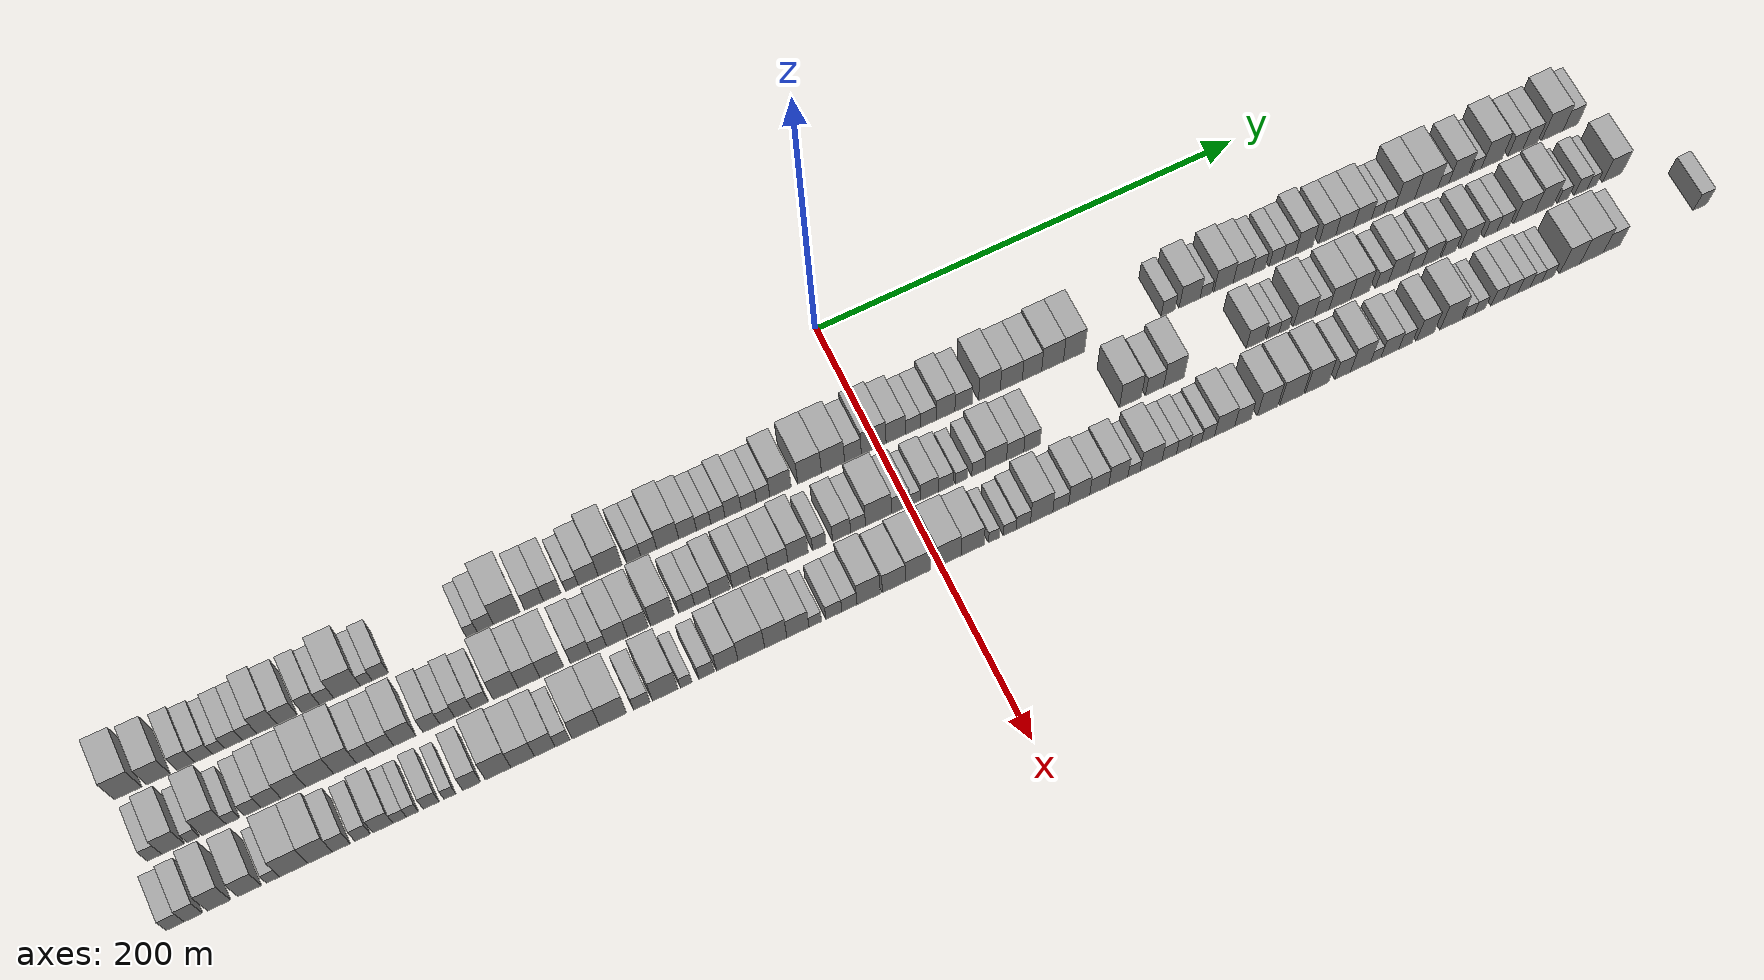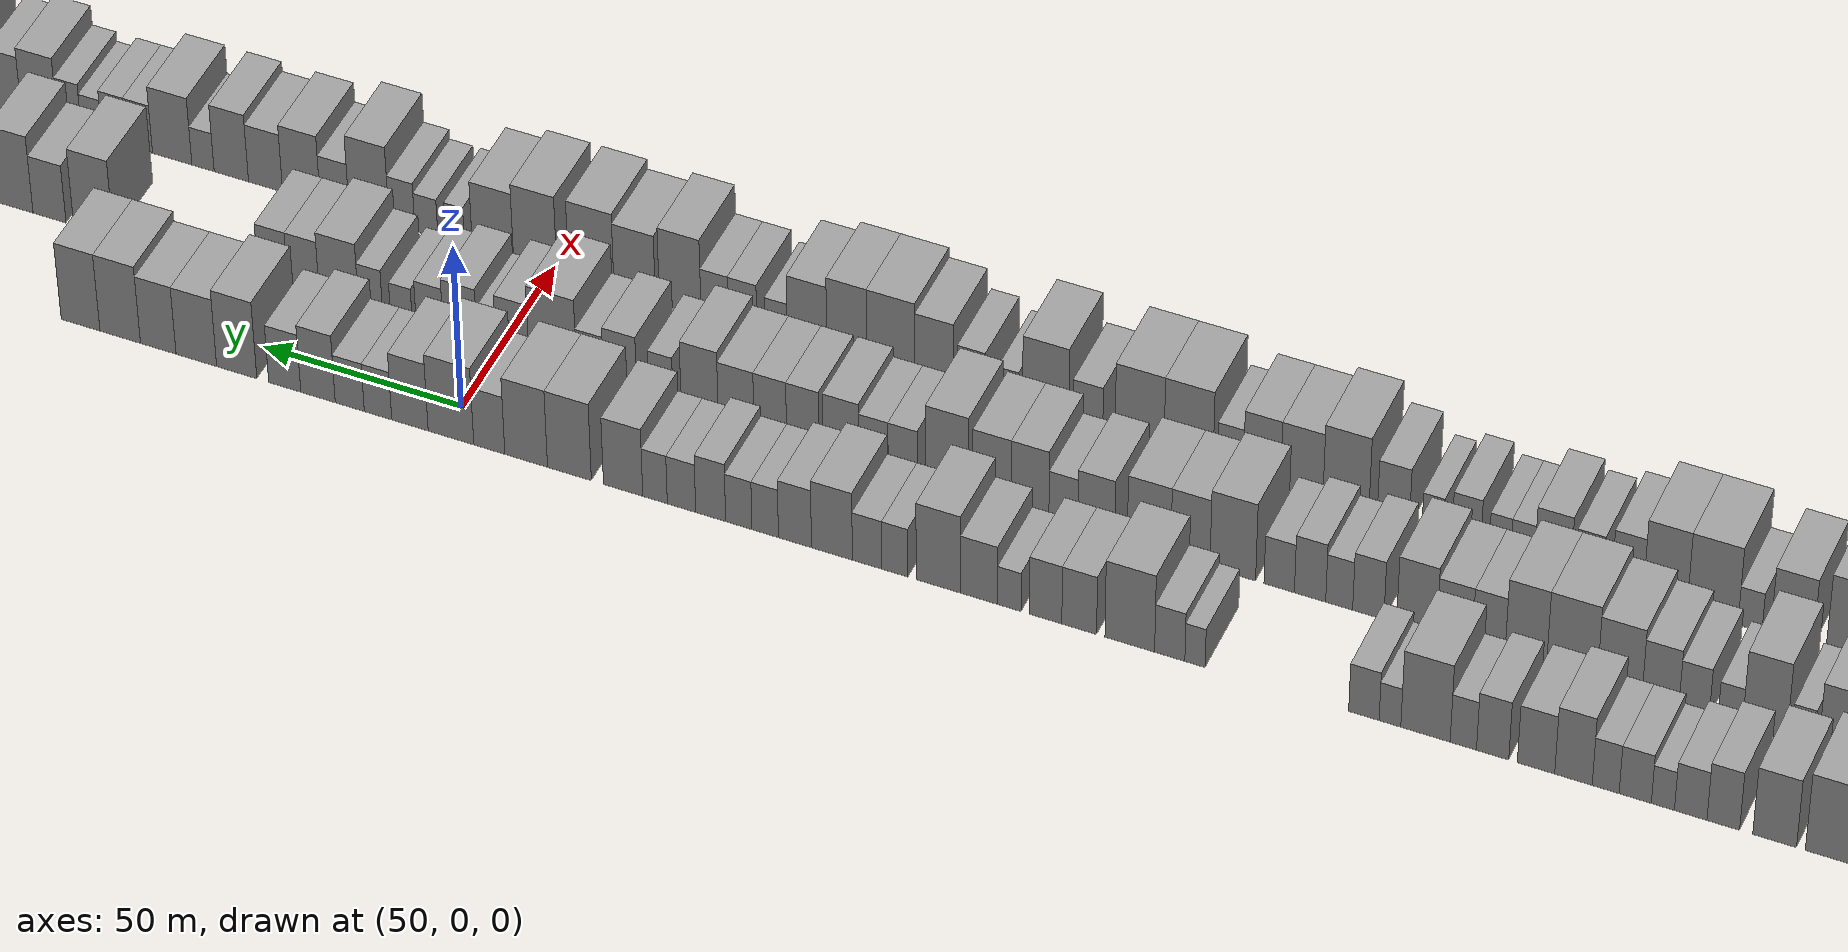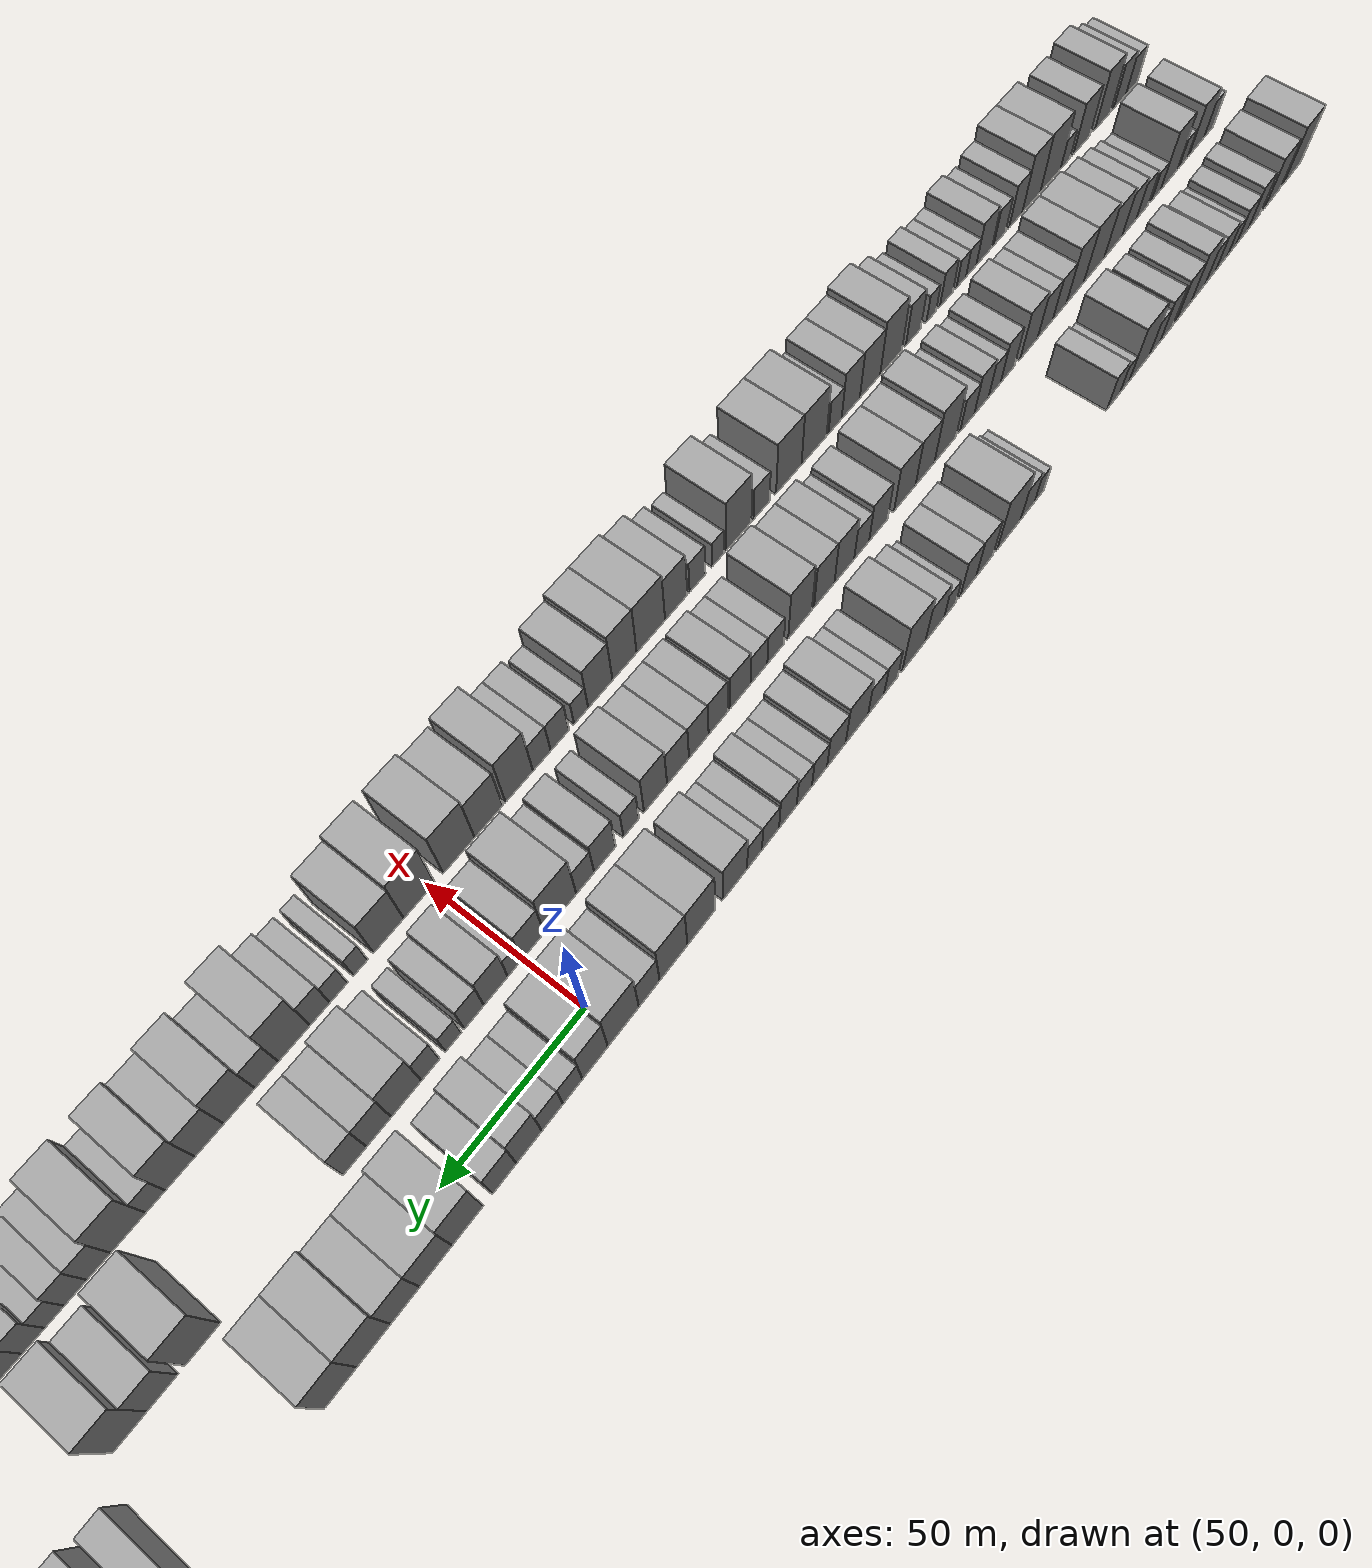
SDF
<sdf version="1.6">
 <world name="default">
  <scene>
   <sky><clouds><speed>12</speed></clouds></sky>
   <ambient>0.4 0.4 0.4 1</ambient>
   <background>0.7 0.7 0.7 1</background>
   <shadows>1</shadows>
  </scene>
  <gravity>0 0 -9.8066</gravity>
  <magnetic_field>6e-06 2.3e-05 -4.2e-05</magnetic_field>
  <physics default="0" name="default_physics" type="ode">
   <ode>
    <solver>
     <type>quick</type>
     <iters>10</iters>
     <sor>1.0</sor>
     <use_dynamic_moi_rescaling>0</use_dynamic_moi_rescaling>
    </solver>
    <constraints>
     <cfm>0</cfm>
     <erp>0.2</erp>
     <contact_max_correcting_vel>100</contact_max_correcting_vel>
     <contact_surface_layer>0.001</contact_surface_layer>
    </constraints>
   </ode>
   <max_step_size>0.004</max_step_size>
   <real_time_factor>1</real_time_factor>
   <real_time_update_rate>250</real_time_update_rate>
  </physics>
  <light name="sun" type="directional">
   <pose>0 0 10 0 0 0</pose>
   <diffuse>0.8 0.8 0.8 1</diffuse>
   <specular>0.2 0.2 0.2 1</specular>
   <attenuation>
    <range>1000</range>
    <constant>0.9</constant>
    <linear>0.01</linear>
    <quadratic>0.001</quadratic>
   </attenuation>
   <direction>-0.5 0.1 -0.9</direction>
  </light>
  <model name="building_1">
   <static>1</static>
   <pose>50.0000 -330.2186 0 0.000000 0.000000 0.000000</pose>
   <link name="link">
    <pose>0 0 12.00 0 0 0</pose>
    <collision name="collision"><geometry><box><size>20.0000 11.5628 24.0000</size></box></geometry></collision>
    <visual name="visual">
     <cast_shadows>0</cast_shadows>
     <geometry><box><size>20.0000 11.5628 24.0000</size></box></geometry>
     <material>
      <script>
       <uri>model://grey_wall/materials/scripts</uri>
       <uri>model://grey_wall/materials/textures</uri>
       <name>vrc/grey_wall</name>
      </script>
     </material>
    </visual>
   </link>
  </model>
  <model name="building_2">
   <static>1</static>
   <pose>50.0000 -317.4556 0 0.000000 0.000000 0.000000</pose>
   <link name="link">
    <pose>0 0 10.50 0 0 0</pose>
    <collision name="collision"><geometry><box><size>20.0000 9.9631 21.0000</size></box></geometry></collision>
    <visual name="visual">
     <cast_shadows>0</cast_shadows>
     <geometry><box><size>20.0000 9.9631 21.0000</size></box></geometry>
     <material>
      <script>
       <uri>model://grey_wall/materials/scripts</uri>
       <uri>model://grey_wall/materials/textures</uri>
       <name>vrc/grey_wall</name>
      </script>
     </material>
    </visual>
   </link>
  </model>
  <model name="building_3">
   <static>1</static>
   <pose>50.0000 -305.7439 0 0.000000 0.000000 0.000000</pose>
   <link name="link">
    <pose>0 0 9.00 0 0 0</pose>
    <collision name="collision"><geometry><box><size>20.0000 7.4604 18.0000</size></box></geometry></collision>
    <visual name="visual">
     <cast_shadows>0</cast_shadows>
     <geometry><box><size>20.0000 7.4604 18.0000</size></box></geometry>
     <material>
      <script>
       <uri>model://grey_wall/materials/scripts</uri>
       <uri>model://grey_wall/materials/textures</uri>
       <name>vrc/grey_wall</name>
      </script>
     </material>
    </visual>
   </link>
  </model>
  <model name="building_4">
   <static>1</static>
   <pose>50.0000 -298.2935 0 0.000000 0.000000 0.000000</pose>
   <link name="link">
    <pose>0 0 7.50 0 0 0</pose>
    <collision name="collision"><geometry><box><size>20.0000 7.4404 15.0000</size></box></geometry></collision>
    <visual name="visual">
     <cast_shadows>0</cast_shadows>
     <geometry><box><size>20.0000 7.4404 15.0000</size></box></geometry>
     <material>
      <script>
       <uri>model://grey_wall/materials/scripts</uri>
       <uri>model://grey_wall/materials/textures</uri>
       <name>vrc/grey_wall</name>
      </script>
     </material>
    </visual>
   </link>
  </model>
  <model name="building_5">
   <static>1</static>
   <pose>50.0000 -291.9311 0 0.000000 0.000000 0.000000</pose>
   <link name="link">
    <pose>0 0 6.00 0 0 0</pose>
    <collision name="collision"><geometry><box><size>20.0000 5.2844 12.0000</size></box></geometry></collision>
    <visual name="visual">
     <cast_shadows>0</cast_shadows>
     <geometry><box><size>20.0000 5.2844 12.0000</size></box></geometry>
     <material>
      <script>
       <uri>model://grey_wall/materials/scripts</uri>
       <uri>model://grey_wall/materials/textures</uri>
       <name>vrc/grey_wall</name>
      </script>
     </material>
    </visual>
   </link>
  </model>
  <model name="building_6">
   <static>1</static>
   <pose>50.0000 -285.5822 0 0.000000 0.000000 0.000000</pose>
   <link name="link">
    <pose>0 0 7.50 0 0 0</pose>
    <collision name="collision"><geometry><box><size>20.0000 7.4134 15.0000</size></box></geometry></collision>
    <visual name="visual">
     <cast_shadows>0</cast_shadows>
     <geometry><box><size>20.0000 7.4134 15.0000</size></box></geometry>
     <material>
      <script>
       <uri>model://grey_wall/materials/scripts</uri>
       <uri>model://grey_wall/materials/textures</uri>
       <name>vrc/grey_wall</name>
      </script>
     </material>
    </visual>
   </link>
  </model>
  <model name="building_7">
   <static>1</static>
   <pose>50.0000 -278.7771 0 0.000000 0.000000 0.000000</pose>
   <link name="link">
    <pose>0 0 7.50 0 0 0</pose>
    <collision name="collision"><geometry><box><size>20.0000 6.1969 15.0000</size></box></geometry></collision>
    <visual name="visual">
     <cast_shadows>0</cast_shadows>
     <geometry><box><size>20.0000 6.1969 15.0000</size></box></geometry>
     <material>
      <script>
       <uri>model://grey_wall/materials/scripts</uri>
       <uri>model://grey_wall/materials/textures</uri>
       <name>vrc/grey_wall</name>
      </script>
     </material>
    </visual>
   </link>
  </model>
  <model name="building_8">
   <static>1</static>
   <pose>50.0000 -271.3484 0 0.000000 0.000000 0.000000</pose>
   <link name="link">
    <pose>0 0 10.50 0 0 0</pose>
    <collision name="collision"><geometry><box><size>20.0000 8.6604 21.0000</size></box></geometry></collision>
    <visual name="visual">
     <cast_shadows>0</cast_shadows>
     <geometry><box><size>20.0000 8.6604 21.0000</size></box></geometry>
     <material>
      <script>
       <uri>model://grey_wall/materials/scripts</uri>
       <uri>model://grey_wall/materials/textures</uri>
       <name>vrc/grey_wall</name>
      </script>
     </material>
    </visual>
   </link>
  </model>
  <model name="building_9">
   <static>1</static>
   <pose>50.0000 -262.6990 0 0.000000 0.000000 0.000000</pose>
   <link name="link">
    <pose>0 0 9.00 0 0 0</pose>
    <collision name="collision"><geometry><box><size>20.0000 8.6385 18.0000</size></box></geometry></collision>
    <visual name="visual">
     <cast_shadows>0</cast_shadows>
     <geometry><box><size>20.0000 8.6385 18.0000</size></box></geometry>
     <material>
      <script>
       <uri>model://grey_wall/materials/scripts</uri>
       <uri>model://grey_wall/materials/textures</uri>
       <name>vrc/grey_wall</name>
      </script>
     </material>
    </visual>
   </link>
  </model>
  <model name="building_10">
   <static>1</static>
   <pose>50.0000 -252.6396 0 0.000000 0.000000 0.000000</pose>
   <link name="link">
    <pose>0 0 9.00 0 0 0</pose>
    <collision name="collision"><geometry><box><size>20.0000 7.4803 18.0000</size></box></geometry></collision>
    <visual name="visual">
     <cast_shadows>0</cast_shadows>
     <geometry><box><size>20.0000 7.4803 18.0000</size></box></geometry>
     <material>
      <script>
       <uri>model://grey_wall/materials/scripts</uri>
       <uri>model://grey_wall/materials/textures</uri>
       <name>vrc/grey_wall</name>
      </script>
     </material>
    </visual>
   </link>
  </model>
  <model name="building_11">
   <static>1</static>
   <pose>50.0000 -245.8336 0 0.000000 0.000000 0.000000</pose>
   <link name="link">
    <pose>0 0 7.50 0 0 0</pose>
    <collision name="collision"><geometry><box><size>20.0000 6.1317 15.0000</size></box></geometry></collision>
    <visual name="visual">
     <cast_shadows>0</cast_shadows>
     <geometry><box><size>20.0000 6.1317 15.0000</size></box></geometry>
     <material>
      <script>
       <uri>model://grey_wall/materials/scripts</uri>
       <uri>model://grey_wall/materials/textures</uri>
       <name>vrc/grey_wall</name>
      </script>
     </material>
    </visual>
   </link>
  </model>
  <model name="building_12">
   <static>1</static>
   <pose>50.0000 -237.0163 0 0.000000 0.000000 0.000000</pose>
   <link name="link">
    <pose>0 0 12.00 0 0 0</pose>
    <collision name="collision"><geometry><box><size>20.0000 11.5029 24.0000</size></box></geometry></collision>
    <visual name="visual">
     <cast_shadows>0</cast_shadows>
     <geometry><box><size>20.0000 11.5029 24.0000</size></box></geometry>
     <material>
      <script>
       <uri>model://grey_wall/materials/scripts</uri>
       <uri>model://grey_wall/materials/textures</uri>
       <name>vrc/grey_wall</name>
      </script>
     </material>
    </visual>
   </link>
  </model>
  <model name="building_13">
   <static>1</static>
   <pose>50.0000 -228.7316 0 0.000000 0.000000 0.000000</pose>
   <link name="link">
    <pose>0 0 6.00 0 0 0</pose>
    <collision name="collision"><geometry><box><size>20.0000 5.0666 12.0000</size></box></geometry></collision>
    <visual name="visual">
     <cast_shadows>0</cast_shadows>
     <geometry><box><size>20.0000 5.0666 12.0000</size></box></geometry>
     <material>
      <script>
       <uri>model://grey_wall/materials/scripts</uri>
       <uri>model://grey_wall/materials/textures</uri>
       <name>vrc/grey_wall</name>
      </script>
     </material>
    </visual>
   </link>
  </model>
  <model name="building_14">
   <static>1</static>
   <pose>50.0000 -222.6365 0 0.000000 0.000000 0.000000</pose>
   <link name="link">
    <pose>0 0 7.50 0 0 0</pose>
    <collision name="collision"><geometry><box><size>20.0000 7.1236 15.0000</size></box></geometry></collision>
    <visual name="visual">
     <cast_shadows>0</cast_shadows>
     <geometry><box><size>20.0000 7.1236 15.0000</size></box></geometry>
     <material>
      <script>
       <uri>model://grey_wall/materials/scripts</uri>
       <uri>model://grey_wall/materials/textures</uri>
       <name>vrc/grey_wall</name>
      </script>
     </material>
    </visual>
   </link>
  </model>
  <model name="building_15">
   <static>1</static>
   <pose>50.0000 -182.8675 0 0.000000 0.000000 0.000000</pose>
   <link name="link">
    <pose>0 0 6.00 0 0 0</pose>
    <collision name="collision"><geometry><box><size>20.0000 4.8048 12.0000</size></box></geometry></collision>
    <visual name="visual">
     <cast_shadows>0</cast_shadows>
     <geometry><box><size>20.0000 4.8048 12.0000</size></box></geometry>
     <material>
      <script>
       <uri>model://grey_wall/materials/scripts</uri>
       <uri>model://grey_wall/materials/textures</uri>
       <name>vrc/grey_wall</name>
      </script>
     </material>
    </visual>
   </link>
  </model>
  <model name="building_16">
   <static>1</static>
   <pose>50.0000 -176.8757 0 0.000000 0.000000 0.000000</pose>
   <link name="link">
    <pose>0 0 7.50 0 0 0</pose>
    <collision name="collision"><geometry><box><size>20.0000 7.1787 15.0000</size></box></geometry></collision>
    <visual name="visual">
     <cast_shadows>0</cast_shadows>
     <geometry><box><size>20.0000 7.1787 15.0000</size></box></geometry>
     <material>
      <script>
       <uri>model://grey_wall/materials/scripts</uri>
       <uri>model://grey_wall/materials/textures</uri>
       <name>vrc/grey_wall</name>
      </script>
     </material>
    </visual>
   </link>
  </model>
  <model name="building_17">
   <static>1</static>
   <pose>50.0000 -167.3817 0 0.000000 0.000000 0.000000</pose>
   <link name="link">
    <pose>0 0 12.00 0 0 0</pose>
    <collision name="collision"><geometry><box><size>20.0000 11.8093 24.0000</size></box></geometry></collision>
    <visual name="visual">
     <cast_shadows>0</cast_shadows>
     <geometry><box><size>20.0000 11.8093 24.0000</size></box></geometry>
     <material>
      <script>
       <uri>model://grey_wall/materials/scripts</uri>
       <uri>model://grey_wall/materials/textures</uri>
       <name>vrc/grey_wall</name>
      </script>
     </material>
    </visual>
   </link>
  </model>
  <model name="building_18">
   <static>1</static>
   <pose>50.0000 -155.3240 0 0.000000 0.000000 0.000000</pose>
   <link name="link">
    <pose>0 0 9.00 0 0 0</pose>
    <collision name="collision"><geometry><box><size>20.0000 8.3063 18.0000</size></box></geometry></collision>
    <visual name="visual">
     <cast_shadows>0</cast_shadows>
     <geometry><box><size>20.0000 8.3063 18.0000</size></box></geometry>
     <material>
      <script>
       <uri>model://grey_wall/materials/scripts</uri>
       <uri>model://grey_wall/materials/textures</uri>
       <name>vrc/grey_wall</name>
      </script>
     </material>
    </visual>
   </link>
  </model>
  <model name="building_19">
   <static>1</static>
   <pose>50.0000 -147.2975 0 0.000000 0.000000 0.000000</pose>
   <link name="link">
    <pose>0 0 9.00 0 0 0</pose>
    <collision name="collision"><geometry><box><size>20.0000 7.7467 18.0000</size></box></geometry></collision>
    <visual name="visual">
     <cast_shadows>0</cast_shadows>
     <geometry><box><size>20.0000 7.7467 18.0000</size></box></geometry>
     <material>
      <script>
       <uri>model://grey_wall/materials/scripts</uri>
       <uri>model://grey_wall/materials/textures</uri>
       <name>vrc/grey_wall</name>
      </script>
     </material>
    </visual>
   </link>
  </model>
  <model name="building_20">
   <static>1</static>
   <pose>50.0000 -138.5946 0 0.000000 0.000000 0.000000</pose>
   <link name="link">
    <pose>0 0 6.00 0 0 0</pose>
    <collision name="collision"><geometry><box><size>20.0000 5.6591 12.0000</size></box></geometry></collision>
    <visual name="visual">
     <cast_shadows>0</cast_shadows>
     <geometry><box><size>20.0000 5.6591 12.0000</size></box></geometry>
     <material>
      <script>
       <uri>model://grey_wall/materials/scripts</uri>
       <uri>model://grey_wall/materials/textures</uri>
       <name>vrc/grey_wall</name>
      </script>
     </material>
    </visual>
   </link>
  </model>
  <model name="building_21">
   <static>1</static>
   <pose>50.0000 -131.3312 0 0.000000 0.000000 0.000000</pose>
   <link name="link">
    <pose>0 0 9.00 0 0 0</pose>
    <collision name="collision"><geometry><box><size>20.0000 8.8676 18.0000</size></box></geometry></collision>
    <visual name="visual">
     <cast_shadows>0</cast_shadows>
     <geometry><box><size>20.0000 8.8676 18.0000</size></box></geometry>
     <material>
      <script>
       <uri>model://grey_wall/materials/scripts</uri>
       <uri>model://grey_wall/materials/textures</uri>
       <name>vrc/grey_wall</name>
      </script>
     </material>
    </visual>
   </link>
  </model>
  <model name="building_22">
   <static>1</static>
   <pose>50.0000 -121.5439 0 0.000000 0.000000 0.000000</pose>
   <link name="link">
    <pose>0 0 12.00 0 0 0</pose>
    <collision name="collision"><geometry><box><size>20.0000 10.7071 24.0000</size></box></geometry></collision>
    <visual name="visual">
     <cast_shadows>0</cast_shadows>
     <geometry><box><size>20.0000 10.7071 24.0000</size></box></geometry>
     <material>
      <script>
       <uri>model://grey_wall/materials/scripts</uri>
       <uri>model://grey_wall/materials/textures</uri>
       <name>vrc/grey_wall</name>
      </script>
     </material>
    </visual>
   </link>
  </model>
  <model name="building_23">
   <static>1</static>
   <pose>50.0000 -111.0377 0 0.000000 0.000000 0.000000</pose>
   <link name="link">
    <pose>0 0 7.50 0 0 0</pose>
    <collision name="collision"><geometry><box><size>20.0000 6.3053 15.0000</size></box></geometry></collision>
    <visual name="visual">
     <cast_shadows>0</cast_shadows>
     <geometry><box><size>20.0000 6.3053 15.0000</size></box></geometry>
     <material>
      <script>
       <uri>model://grey_wall/materials/scripts</uri>
       <uri>model://grey_wall/materials/textures</uri>
       <name>vrc/grey_wall</name>
      </script>
     </material>
    </visual>
   </link>
  </model>
  <model name="building_24">
   <static>1</static>
   <pose>50.0000 -104.3092 0 0.000000 0.000000 0.000000</pose>
   <link name="link">
    <pose>0 0 7.50 0 0 0</pose>
    <collision name="collision"><geometry><box><size>20.0000 7.1516 15.0000</size></box></geometry></collision>
    <visual name="visual">
     <cast_shadows>0</cast_shadows>
     <geometry><box><size>20.0000 7.1516 15.0000</size></box></geometry>
     <material>
      <script>
       <uri>model://grey_wall/materials/scripts</uri>
       <uri>model://grey_wall/materials/textures</uri>
       <name>vrc/grey_wall</name>
      </script>
     </material>
    </visual>
   </link>
  </model>
  <model name="building_25">
   <static>1</static>
   <pose>50.0000 -95.7648 0 0.000000 0.000000 0.000000</pose>
   <link name="link">
    <pose>0 0 10.50 0 0 0</pose>
    <collision name="collision"><geometry><box><size>20.0000 9.9373 21.0000</size></box></geometry></collision>
    <visual name="visual">
     <cast_shadows>0</cast_shadows>
     <geometry><box><size>20.0000 9.9373 21.0000</size></box></geometry>
     <material>
      <script>
       <uri>model://grey_wall/materials/scripts</uri>
       <uri>model://grey_wall/materials/textures</uri>
       <name>vrc/grey_wall</name>
      </script>
     </material>
    </visual>
   </link>
  </model>
  <model name="building_26">
   <static>1</static>
   <pose>50.0000 -86.7665 0 0.000000 0.000000 0.000000</pose>
   <link name="link">
    <pose>0 0 9.00 0 0 0</pose>
    <collision name="collision"><geometry><box><size>20.0000 8.0591 18.0000</size></box></geometry></collision>
    <visual name="visual">
     <cast_shadows>0</cast_shadows>
     <geometry><box><size>20.0000 8.0591 18.0000</size></box></geometry>
     <material>
      <script>
       <uri>model://grey_wall/materials/scripts</uri>
       <uri>model://grey_wall/materials/textures</uri>
       <name>vrc/grey_wall</name>
      </script>
     </material>
    </visual>
   </link>
  </model>
  <model name="building_27">
   <static>1</static>
   <pose>50.0000 -79.5064 0 0.000000 0.000000 0.000000</pose>
   <link name="link">
    <pose>0 0 7.50 0 0 0</pose>
    <collision name="collision"><geometry><box><size>20.0000 6.4612 15.0000</size></box></geometry></collision>
    <visual name="visual">
     <cast_shadows>0</cast_shadows>
     <geometry><box><size>20.0000 6.4612 15.0000</size></box></geometry>
     <material>
      <script>
       <uri>model://grey_wall/materials/scripts</uri>
       <uri>model://grey_wall/materials/textures</uri>
       <name>vrc/grey_wall</name>
      </script>
     </material>
    </visual>
   </link>
  </model>
  <model name="building_28">
   <static>1</static>
   <pose>50.0000 -73.0617 0 0.000000 0.000000 0.000000</pose>
   <link name="link">
    <pose>0 0 7.50 0 0 0</pose>
    <collision name="collision"><geometry><box><size>20.0000 6.4282 15.0000</size></box></geometry></collision>
    <visual name="visual">
     <cast_shadows>0</cast_shadows>
     <geometry><box><size>20.0000 6.4282 15.0000</size></box></geometry>
     <material>
      <script>
       <uri>model://grey_wall/materials/scripts</uri>
       <uri>model://grey_wall/materials/textures</uri>
       <name>vrc/grey_wall</name>
      </script>
     </material>
    </visual>
   </link>
  </model>
  <model name="building_29">
   <static>1</static>
   <pose>50.0000 -66.1750 0 0.000000 0.000000 0.000000</pose>
   <link name="link">
    <pose>0 0 9.00 0 0 0</pose>
    <collision name="collision"><geometry><box><size>20.0000 7.3453 18.0000</size></box></geometry></collision>
    <visual name="visual">
     <cast_shadows>0</cast_shadows>
     <geometry><box><size>20.0000 7.3453 18.0000</size></box></geometry>
     <material>
      <script>
       <uri>model://grey_wall/materials/scripts</uri>
       <uri>model://grey_wall/materials/textures</uri>
       <name>vrc/grey_wall</name>
      </script>
     </material>
    </visual>
   </link>
  </model>
  <model name="building_30">
   <static>1</static>
   <pose>50.0000 -59.0148 0 0.000000 0.000000 0.000000</pose>
   <link name="link">
    <pose>0 0 7.50 0 0 0</pose>
    <collision name="collision"><geometry><box><size>20.0000 6.9750 15.0000</size></box></geometry></collision>
    <visual name="visual">
     <cast_shadows>0</cast_shadows>
     <geometry><box><size>20.0000 6.9750 15.0000</size></box></geometry>
     <material>
      <script>
       <uri>model://grey_wall/materials/scripts</uri>
       <uri>model://grey_wall/materials/textures</uri>
       <name>vrc/grey_wall</name>
      </script>
     </material>
    </visual>
   </link>
  </model>
  <model name="building_31">
   <static>1</static>
   <pose>50.0000 -52.5068 0 0.000000 0.000000 0.000000</pose>
   <link name="link">
    <pose>0 0 7.50 0 0 0</pose>
    <collision name="collision"><geometry><box><size>20.0000 6.0411 15.0000</size></box></geometry></collision>
    <visual name="visual">
     <cast_shadows>0</cast_shadows>
     <geometry><box><size>20.0000 6.0411 15.0000</size></box></geometry>
     <material>
      <script>
       <uri>model://grey_wall/materials/scripts</uri>
       <uri>model://grey_wall/materials/textures</uri>
       <name>vrc/grey_wall</name>
      </script>
     </material>
    </visual>
   </link>
  </model>
  <model name="building_32">
   <static>1</static>
   <pose>50.0000 -44.6424 0 0.000000 0.000000 0.000000</pose>
   <link name="link">
    <pose>0 0 10.50 0 0 0</pose>
    <collision name="collision"><geometry><box><size>20.0000 9.6876 21.0000</size></box></geometry></collision>
    <visual name="visual">
     <cast_shadows>0</cast_shadows>
     <geometry><box><size>20.0000 9.6876 21.0000</size></box></geometry>
     <material>
      <script>
       <uri>model://grey_wall/materials/scripts</uri>
       <uri>model://grey_wall/materials/textures</uri>
       <name>vrc/grey_wall</name>
      </script>
     </material>
    </visual>
   </link>
  </model>
  <model name="building_33">
   <static>1</static>
   <pose>50.0000 -31.3701 0 0.000000 0.000000 0.000000</pose>
   <link name="link">
    <pose>0 0 12.00 0 0 0</pose>
    <collision name="collision"><geometry><box><size>20.0000 10.8570 24.0000</size></box></geometry></collision>
    <visual name="visual">
     <cast_shadows>0</cast_shadows>
     <geometry><box><size>20.0000 10.8570 24.0000</size></box></geometry>
     <material>
      <script>
       <uri>model://grey_wall/materials/scripts</uri>
       <uri>model://grey_wall/materials/textures</uri>
       <name>vrc/grey_wall</name>
      </script>
     </material>
    </visual>
   </link>
  </model>
  <model name="building_34">
   <static>1</static>
   <pose>50.0000 -20.6440 0 0.000000 0.000000 0.000000</pose>
   <link name="link">
    <pose>0 0 12.00 0 0 0</pose>
    <collision name="collision"><geometry><box><size>20.0000 10.5951 24.0000</size></box></geometry></collision>
    <visual name="visual">
     <cast_shadows>0</cast_shadows>
     <geometry><box><size>20.0000 10.5951 24.0000</size></box></geometry>
     <material>
      <script>
       <uri>model://grey_wall/materials/scripts</uri>
       <uri>model://grey_wall/materials/textures</uri>
       <name>vrc/grey_wall</name>
      </script>
     </material>
    </visual>
   </link>
  </model>
  <model name="building_35">
   <static>1</static>
   <pose>50.0000 -11.4797 0 0.000000 0.000000 0.000000</pose>
   <link name="link">
    <pose>0 0 9.00 0 0 0</pose>
    <collision name="collision"><geometry><box><size>20.0000 7.7335 18.0000</size></box></geometry></collision>
    <visual name="visual">
     <cast_shadows>0</cast_shadows>
     <geometry><box><size>20.0000 7.7335 18.0000</size></box></geometry>
     <material>
      <script>
       <uri>model://grey_wall/materials/scripts</uri>
       <uri>model://grey_wall/materials/textures</uri>
       <name>vrc/grey_wall</name>
      </script>
     </material>
    </visual>
   </link>
  </model>
  <model name="building_36">
   <static>1</static>
   <pose>50.0000 -1.9124 0 0.000000 0.000000 0.000000</pose>
   <link name="link">
    <pose>0 0 12.00 0 0 0</pose>
    <collision name="collision"><geometry><box><size>20.0000 11.4013 24.0000</size></box></geometry></collision>
    <visual name="visual">
     <cast_shadows>0</cast_shadows>
     <geometry><box><size>20.0000 11.4013 24.0000</size></box></geometry>
     <material>
      <script>
       <uri>model://grey_wall/materials/scripts</uri>
       <uri>model://grey_wall/materials/textures</uri>
       <name>vrc/grey_wall</name>
      </script>
     </material>
    </visual>
   </link>
  </model>
  <model name="building_37">
   <static>1</static>
   <pose>50.0000 8.3407 0 0.000000 0.000000 0.000000</pose>
   <link name="link">
    <pose>0 0 10.50 0 0 0</pose>
    <collision name="collision"><geometry><box><size>20.0000 9.1049 21.0000</size></box></geometry></collision>
    <visual name="visual">
     <cast_shadows>0</cast_shadows>
     <geometry><box><size>20.0000 9.1049 21.0000</size></box></geometry>
     <material>
      <script>
       <uri>model://grey_wall/materials/scripts</uri>
       <uri>model://grey_wall/materials/textures</uri>
       <name>vrc/grey_wall</name>
      </script>
     </material>
    </visual>
   </link>
  </model>
  <model name="building_38">
   <static>1</static>
   <pose>50.0000 16.3388 0 0.000000 0.000000 0.000000</pose>
   <link name="link">
    <pose>0 0 7.50 0 0 0</pose>
    <collision name="collision"><geometry><box><size>20.0000 6.8914 15.0000</size></box></geometry></collision>
    <visual name="visual">
     <cast_shadows>0</cast_shadows>
     <geometry><box><size>20.0000 6.8914 15.0000</size></box></geometry>
     <material>
      <script>
       <uri>model://grey_wall/materials/scripts</uri>
       <uri>model://grey_wall/materials/textures</uri>
       <name>vrc/grey_wall</name>
      </script>
     </material>
    </visual>
   </link>
  </model>
  <model name="building_39">
   <static>1</static>
   <pose>50.0000 23.4377 0 0.000000 0.000000 0.000000</pose>
   <link name="link">
    <pose>0 0 7.50 0 0 0</pose>
    <collision name="collision"><geometry><box><size>20.0000 7.3063 15.0000</size></box></geometry></collision>
    <visual name="visual">
     <cast_shadows>0</cast_shadows>
     <geometry><box><size>20.0000 7.3063 15.0000</size></box></geometry>
     <material>
      <script>
       <uri>model://grey_wall/materials/scripts</uri>
       <uri>model://grey_wall/materials/textures</uri>
       <name>vrc/grey_wall</name>
      </script>
     </material>
    </visual>
   </link>
  </model>
  <model name="building_40">
   <static>1</static>
   <pose>50.0000 31.4318 0 0.000000 0.000000 0.000000</pose>
   <link name="link">
    <pose>0 0 10.50 0 0 0</pose>
    <collision name="collision"><geometry><box><size>20.0000 8.6821 21.0000</size></box></geometry></collision>
    <visual name="visual">
     <cast_shadows>0</cast_shadows>
     <geometry><box><size>20.0000 8.6821 21.0000</size></box></geometry>
     <material>
      <script>
       <uri>model://grey_wall/materials/scripts</uri>
       <uri>model://grey_wall/materials/textures</uri>
       <name>vrc/grey_wall</name>
      </script>
     </material>
    </visual>
   </link>
  </model>
  <model name="building_41">
   <static>1</static>
   <pose>50.0000 39.8269 0 0.000000 0.000000 0.000000</pose>
   <link name="link">
    <pose>0 0 9.00 0 0 0</pose>
    <collision name="collision"><geometry><box><size>20.0000 8.1081 18.0000</size></box></geometry></collision>
    <visual name="visual">
     <cast_shadows>0</cast_shadows>
     <geometry><box><size>20.0000 8.1081 18.0000</size></box></geometry>
     <material>
      <script>
       <uri>model://grey_wall/materials/scripts</uri>
       <uri>model://grey_wall/materials/textures</uri>
       <name>vrc/grey_wall</name>
      </script>
     </material>
    </visual>
   </link>
  </model>
  <model name="building_42">
   <static>1</static>
   <pose>50.0000 51.9822 0 0.000000 0.000000 0.000000</pose>
   <link name="link">
    <pose>0 0 12.00 0 0 0</pose>
    <collision name="collision"><geometry><box><size>20.0000 10.2024 24.0000</size></box></geometry></collision>
    <visual name="visual">
     <cast_shadows>0</cast_shadows>
     <geometry><box><size>20.0000 10.2024 24.0000</size></box></geometry>
     <material>
      <script>
       <uri>model://grey_wall/materials/scripts</uri>
       <uri>model://grey_wall/materials/textures</uri>
       <name>vrc/grey_wall</name>
      </script>
     </material>
    </visual>
   </link>
  </model>
  <model name="building_43">
   <static>1</static>
   <pose>50.0000 62.2492 0 0.000000 0.000000 0.000000</pose>
   <link name="link">
    <pose>0 0 10.50 0 0 0</pose>
    <collision name="collision"><geometry><box><size>20.0000 10.3316 21.0000</size></box></geometry></collision>
    <visual name="visual">
     <cast_shadows>0</cast_shadows>
     <geometry><box><size>20.0000 10.3316 21.0000</size></box></geometry>
     <material>
      <script>
       <uri>model://grey_wall/materials/scripts</uri>
       <uri>model://grey_wall/materials/textures</uri>
       <name>vrc/grey_wall</name>
      </script>
     </material>
    </visual>
   </link>
  </model>
  <model name="building_44">
   <static>1</static>
   <pose>50.0000 71.9521 0 0.000000 0.000000 0.000000</pose>
   <link name="link">
    <pose>0 0 10.50 0 0 0</pose>
    <collision name="collision"><geometry><box><size>20.0000 9.0741 21.0000</size></box></geometry></collision>
    <visual name="visual">
     <cast_shadows>0</cast_shadows>
     <geometry><box><size>20.0000 9.0741 21.0000</size></box></geometry>
     <material>
      <script>
       <uri>model://grey_wall/materials/scripts</uri>
       <uri>model://grey_wall/materials/textures</uri>
       <name>vrc/grey_wall</name>
      </script>
     </material>
    </visual>
   </link>
  </model>
  <model name="building_45">
   <static>1</static>
   <pose>50.0000 81.6699 0 0.000000 0.000000 0.000000</pose>
   <link name="link">
    <pose>0 0 12.00 0 0 0</pose>
    <collision name="collision"><geometry><box><size>20.0000 10.3615 24.0000</size></box></geometry></collision>
    <visual name="visual">
     <cast_shadows>0</cast_shadows>
     <geometry><box><size>20.0000 10.3615 24.0000</size></box></geometry>
     <material>
      <script>
       <uri>model://grey_wall/materials/scripts</uri>
       <uri>model://grey_wall/materials/textures</uri>
       <name>vrc/grey_wall</name>
      </script>
     </material>
    </visual>
   </link>
  </model>
  <model name="building_46">
   <static>1</static>
   <pose>50.0000 91.8081 0 0.000000 0.000000 0.000000</pose>
   <link name="link">
    <pose>0 0 12.00 0 0 0</pose>
    <collision name="collision"><geometry><box><size>20.0000 9.9149 24.0000</size></box></geometry></collision>
    <visual name="visual">
     <cast_shadows>0</cast_shadows>
     <geometry><box><size>20.0000 9.9149 24.0000</size></box></geometry>
     <material>
      <script>
       <uri>model://grey_wall/materials/scripts</uri>
       <uri>model://grey_wall/materials/textures</uri>
       <name>vrc/grey_wall</name>
      </script>
     </material>
    </visual>
   </link>
  </model>
  <model name="building_47">
   <static>1</static>
   <pose>50.0000 136.7579 0 0.000000 0.000000 0.000000</pose>
   <link name="link">
    <pose>0 0 7.50 0 0 0</pose>
    <collision name="collision"><geometry><box><size>20.0000 6.6616 15.0000</size></box></geometry></collision>
    <visual name="visual">
     <cast_shadows>0</cast_shadows>
     <geometry><box><size>20.0000 6.6616 15.0000</size></box></geometry>
     <material>
      <script>
       <uri>model://grey_wall/materials/scripts</uri>
       <uri>model://grey_wall/materials/textures</uri>
       <name>vrc/grey_wall</name>
      </script>
     </material>
    </visual>
   </link>
  </model>
  <model name="building_48">
   <static>1</static>
   <pose>50.0000 147.1466 0 0.000000 0.000000 0.000000</pose>
   <link name="link">
    <pose>0 0 10.50 0 0 0</pose>
    <collision name="collision"><geometry><box><size>20.0000 10.1159 21.0000</size></box></geometry></collision>
    <visual name="visual">
     <cast_shadows>0</cast_shadows>
     <geometry><box><size>20.0000 10.1159 21.0000</size></box></geometry>
     <material>
      <script>
       <uri>model://grey_wall/materials/scripts</uri>
       <uri>model://grey_wall/materials/textures</uri>
       <name>vrc/grey_wall</name>
      </script>
     </material>
    </visual>
   </link>
  </model>
  <model name="building_49">
   <static>1</static>
   <pose>50.0000 155.0259 0 0.000000 0.000000 0.000000</pose>
   <link name="link">
    <pose>0 0 6.00 0 0 0</pose>
    <collision name="collision"><geometry><box><size>20.0000 5.6427 12.0000</size></box></geometry></collision>
    <visual name="visual">
     <cast_shadows>0</cast_shadows>
     <geometry><box><size>20.0000 5.6427 12.0000</size></box></geometry>
     <material>
      <script>
       <uri>model://grey_wall/materials/scripts</uri>
       <uri>model://grey_wall/materials/textures</uri>
       <name>vrc/grey_wall</name>
      </script>
     </material>
    </visual>
   </link>
  </model>
  <model name="building_50">
   <static>1</static>
   <pose>50.0000 163.5121 0 0.000000 0.000000 0.000000</pose>
   <link name="link">
    <pose>0 0 10.50 0 0 0</pose>
    <collision name="collision"><geometry><box><size>20.0000 9.3296 21.0000</size></box></geometry></collision>
    <visual name="visual">
     <cast_shadows>0</cast_shadows>
     <geometry><box><size>20.0000 9.3296 21.0000</size></box></geometry>
     <material>
      <script>
       <uri>model://grey_wall/materials/scripts</uri>
       <uri>model://grey_wall/materials/textures</uri>
       <name>vrc/grey_wall</name>
      </script>
     </material>
    </visual>
   </link>
  </model>
  <model name="building_51">
   <static>1</static>
   <pose>50.0000 172.6327 0 0.000000 0.000000 0.000000</pose>
   <link name="link">
    <pose>0 0 9.00 0 0 0</pose>
    <collision name="collision"><geometry><box><size>20.0000 8.9117 18.0000</size></box></geometry></collision>
    <visual name="visual">
     <cast_shadows>0</cast_shadows>
     <geometry><box><size>20.0000 8.9117 18.0000</size></box></geometry>
     <material>
      <script>
       <uri>model://grey_wall/materials/scripts</uri>
       <uri>model://grey_wall/materials/textures</uri>
       <name>vrc/grey_wall</name>
      </script>
     </material>
    </visual>
   </link>
  </model>
  <model name="building_52">
   <static>1</static>
   <pose>50.0000 180.3997 0 0.000000 0.000000 0.000000</pose>
   <link name="link">
    <pose>0 0 7.50 0 0 0</pose>
    <collision name="collision"><geometry><box><size>20.0000 6.6225 15.0000</size></box></geometry></collision>
    <visual name="visual">
     <cast_shadows>0</cast_shadows>
     <geometry><box><size>20.0000 6.6225 15.0000</size></box></geometry>
     <material>
      <script>
       <uri>model://grey_wall/materials/scripts</uri>
       <uri>model://grey_wall/materials/textures</uri>
       <name>vrc/grey_wall</name>
      </script>
     </material>
    </visual>
   </link>
  </model>
  <model name="building_53">
   <static>1</static>
   <pose>50.0000 188.8815 0 0.000000 0.000000 0.000000</pose>
   <link name="link">
    <pose>0 0 7.50 0 0 0</pose>
    <collision name="collision"><geometry><box><size>20.0000 6.3411 15.0000</size></box></geometry></collision>
    <visual name="visual">
     <cast_shadows>0</cast_shadows>
     <geometry><box><size>20.0000 6.3411 15.0000</size></box></geometry>
     <material>
      <script>
       <uri>model://grey_wall/materials/scripts</uri>
       <uri>model://grey_wall/materials/textures</uri>
       <name>vrc/grey_wall</name>
      </script>
     </material>
    </visual>
   </link>
  </model>
  <model name="building_54">
   <static>1</static>
   <pose>50.0000 195.2302 0 0.000000 0.000000 0.000000</pose>
   <link name="link">
    <pose>0 0 7.50 0 0 0</pose>
    <collision name="collision"><geometry><box><size>20.0000 6.3562 15.0000</size></box></geometry></collision>
    <visual name="visual">
     <cast_shadows>0</cast_shadows>
     <geometry><box><size>20.0000 6.3562 15.0000</size></box></geometry>
     <material>
      <script>
       <uri>model://grey_wall/materials/scripts</uri>
       <uri>model://grey_wall/materials/textures</uri>
       <name>vrc/grey_wall</name>
      </script>
     </material>
    </visual>
   </link>
  </model>
  <model name="building_55">
   <static>1</static>
   <pose>50.0000 202.6620 0 0.000000 0.000000 0.000000</pose>
   <link name="link">
    <pose>0 0 10.50 0 0 0</pose>
    <collision name="collision"><geometry><box><size>20.0000 8.5074 21.0000</size></box></geometry></collision>
    <visual name="visual">
     <cast_shadows>0</cast_shadows>
     <geometry><box><size>20.0000 8.5074 21.0000</size></box></geometry>
     <material>
      <script>
       <uri>model://grey_wall/materials/scripts</uri>
       <uri>model://grey_wall/materials/textures</uri>
       <name>vrc/grey_wall</name>
      </script>
     </material>
    </visual>
   </link>
  </model>
  <model name="building_56">
   <static>1</static>
   <pose>50.0000 214.0242 0 0.000000 0.000000 0.000000</pose>
   <link name="link">
    <pose>0 0 9.00 0 0 0</pose>
    <collision name="collision"><geometry><box><size>20.0000 8.2172 18.0000</size></box></geometry></collision>
    <visual name="visual">
     <cast_shadows>0</cast_shadows>
     <geometry><box><size>20.0000 8.2172 18.0000</size></box></geometry>
     <material>
      <script>
       <uri>model://grey_wall/materials/scripts</uri>
       <uri>model://grey_wall/materials/textures</uri>
       <name>vrc/grey_wall</name>
      </script>
     </material>
    </visual>
   </link>
  </model>
  <model name="building_57">
   <static>1</static>
   <pose>50.0000 222.5899 0 0.000000 0.000000 0.000000</pose>
   <link name="link">
    <pose>0 0 9.00 0 0 0</pose>
    <collision name="collision"><geometry><box><size>20.0000 8.9143 18.0000</size></box></geometry></collision>
    <visual name="visual">
     <cast_shadows>0</cast_shadows>
     <geometry><box><size>20.0000 8.9143 18.0000</size></box></geometry>
     <material>
      <script>
       <uri>model://grey_wall/materials/scripts</uri>
       <uri>model://grey_wall/materials/textures</uri>
       <name>vrc/grey_wall</name>
      </script>
     </material>
    </visual>
   </link>
  </model>
  <model name="building_58">
   <static>1</static>
   <pose>50.0000 231.4520 0 0.000000 0.000000 0.000000</pose>
   <link name="link">
    <pose>0 0 9.00 0 0 0</pose>
    <collision name="collision"><geometry><box><size>20.0000 8.8098 18.0000</size></box></geometry></collision>
    <visual name="visual">
     <cast_shadows>0</cast_shadows>
     <geometry><box><size>20.0000 8.8098 18.0000</size></box></geometry>
     <material>
      <script>
       <uri>model://grey_wall/materials/scripts</uri>
       <uri>model://grey_wall/materials/textures</uri>
       <name>vrc/grey_wall</name>
      </script>
     </material>
    </visual>
   </link>
  </model>
  <model name="building_59">
   <static>1</static>
   <pose>50.0000 238.7716 0 0.000000 0.000000 0.000000</pose>
   <link name="link">
    <pose>0 0 6.00 0 0 0</pose>
    <collision name="collision"><geometry><box><size>20.0000 5.8293 12.0000</size></box></geometry></collision>
    <visual name="visual">
     <cast_shadows>0</cast_shadows>
     <geometry><box><size>20.0000 5.8293 12.0000</size></box></geometry>
     <material>
      <script>
       <uri>model://grey_wall/materials/scripts</uri>
       <uri>model://grey_wall/materials/textures</uri>
       <name>vrc/grey_wall</name>
      </script>
     </material>
    </visual>
   </link>
  </model>
  <model name="building_60">
   <static>1</static>
   <pose>50.0000 244.5760 0 0.000000 0.000000 0.000000</pose>
   <link name="link">
    <pose>0 0 6.00 0 0 0</pose>
    <collision name="collision"><geometry><box><size>20.0000 5.7796 12.0000</size></box></geometry></collision>
    <visual name="visual">
     <cast_shadows>0</cast_shadows>
     <geometry><box><size>20.0000 5.7796 12.0000</size></box></geometry>
     <material>
      <script>
       <uri>model://grey_wall/materials/scripts</uri>
       <uri>model://grey_wall/materials/textures</uri>
       <name>vrc/grey_wall</name>
      </script>
     </material>
    </visual>
   </link>
  </model>
  <model name="building_61">
   <static>1</static>
   <pose>50.0000 252.3207 0 0.000000 0.000000 0.000000</pose>
   <link name="link">
    <pose>0 0 12.00 0 0 0</pose>
    <collision name="collision"><geometry><box><size>20.0000 9.7096 24.0000</size></box></geometry></collision>
    <visual name="visual">
     <cast_shadows>0</cast_shadows>
     <geometry><box><size>20.0000 9.7096 24.0000</size></box></geometry>
     <material>
      <script>
       <uri>model://grey_wall/materials/scripts</uri>
       <uri>model://grey_wall/materials/textures</uri>
       <name>vrc/grey_wall</name>
      </script>
     </material>
    </visual>
   </link>
  </model>
  <model name="building_62">
   <static>1</static>
   <pose>50.0000 262.9790 0 0.000000 0.000000 0.000000</pose>
   <link name="link">
    <pose>0 0 12.00 0 0 0</pose>
    <collision name="collision"><geometry><box><size>20.0000 11.6071 24.0000</size></box></geometry></collision>
    <visual name="visual">
     <cast_shadows>0</cast_shadows>
     <geometry><box><size>20.0000 11.6071 24.0000</size></box></geometry>
     <material>
      <script>
       <uri>model://grey_wall/materials/scripts</uri>
       <uri>model://grey_wall/materials/textures</uri>
       <name>vrc/grey_wall</name>
      </script>
     </material>
    </visual>
   </link>
  </model>
  <model name="building_63">
   <static>1</static>
   <pose>50.0000 271.5103 0 0.000000 0.000000 0.000000</pose>
   <link name="link">
    <pose>0 0 6.00 0 0 0</pose>
    <collision name="collision"><geometry><box><size>20.0000 5.4555 12.0000</size></box></geometry></collision>
    <visual name="visual">
     <cast_shadows>0</cast_shadows>
     <geometry><box><size>20.0000 5.4555 12.0000</size></box></geometry>
     <material>
      <script>
       <uri>model://grey_wall/materials/scripts</uri>
       <uri>model://grey_wall/materials/textures</uri>
       <name>vrc/grey_wall</name>
      </script>
     </material>
    </visual>
   </link>
  </model>
  <model name="building_64">
   <static>1</static>
   <pose>50.0000 279.2497 0 0.000000 0.000000 0.000000</pose>
   <link name="link">
    <pose>0 0 10.50 0 0 0</pose>
    <collision name="collision"><geometry><box><size>20.0000 10.0232 21.0000</size></box></geometry></collision>
    <visual name="visual">
     <cast_shadows>0</cast_shadows>
     <geometry><box><size>20.0000 10.0232 21.0000</size></box></geometry>
     <material>
      <script>
       <uri>model://grey_wall/materials/scripts</uri>
       <uri>model://grey_wall/materials/textures</uri>
       <name>vrc/grey_wall</name>
      </script>
     </material>
    </visual>
   </link>
  </model>
  <model name="building_65">
   <static>1</static>
   <pose>50.0000 287.9108 0 0.000000 0.000000 0.000000</pose>
   <link name="link">
    <pose>0 0 6.00 0 0 0</pose>
    <collision name="collision"><geometry><box><size>20.0000 5.2991 12.0000</size></box></geometry></collision>
    <visual name="visual">
     <cast_shadows>0</cast_shadows>
     <geometry><box><size>20.0000 5.2991 12.0000</size></box></geometry>
     <material>
      <script>
       <uri>model://grey_wall/materials/scripts</uri>
       <uri>model://grey_wall/materials/textures</uri>
       <name>vrc/grey_wall</name>
      </script>
     </material>
    </visual>
   </link>
  </model>
  <model name="building_66">
   <static>1</static>
   <pose>50.0000 295.7887 0 0.000000 0.000000 0.000000</pose>
   <link name="link">
    <pose>0 0 12.00 0 0 0</pose>
    <collision name="collision"><geometry><box><size>20.0000 10.4567 24.0000</size></box></geometry></collision>
    <visual name="visual">
     <cast_shadows>0</cast_shadows>
     <geometry><box><size>20.0000 10.4567 24.0000</size></box></geometry>
     <material>
      <script>
       <uri>model://grey_wall/materials/scripts</uri>
       <uri>model://grey_wall/materials/textures</uri>
       <name>vrc/grey_wall</name>
      </script>
     </material>
    </visual>
   </link>
  </model>
  <model name="building_67">
   <static>1</static>
   <pose>50.0000 307.7833 0 0.000000 0.000000 0.000000</pose>
   <link name="link">
    <pose>0 0 9.00 0 0 0</pose>
    <collision name="collision"><geometry><box><size>20.0000 7.5326 18.0000</size></box></geometry></collision>
    <visual name="visual">
     <cast_shadows>0</cast_shadows>
     <geometry><box><size>20.0000 7.5326 18.0000</size></box></geometry>
     <material>
      <script>
       <uri>model://grey_wall/materials/scripts</uri>
       <uri>model://grey_wall/materials/textures</uri>
       <name>vrc/grey_wall</name>
      </script>
     </material>
    </visual>
   </link>
  </model>
  <model name="building_68">
   <static>1</static>
   <pose>50.0000 315.2101 0 0.000000 0.000000 0.000000</pose>
   <link name="link">
    <pose>0 0 9.00 0 0 0</pose>
    <collision name="collision"><geometry><box><size>20.0000 7.3210 18.0000</size></box></geometry></collision>
    <visual name="visual">
     <cast_shadows>0</cast_shadows>
     <geometry><box><size>20.0000 7.3210 18.0000</size></box></geometry>
     <material>
      <script>
       <uri>model://grey_wall/materials/scripts</uri>
       <uri>model://grey_wall/materials/textures</uri>
       <name>vrc/grey_wall</name>
      </script>
     </material>
    </visual>
   </link>
  </model>
  <model name="building_69">
   <static>1</static>
   <pose>50.0000 326.3032 0 0.000000 0.000000 0.000000</pose>
   <link name="link">
    <pose>0 0 12.00 0 0 0</pose>
    <collision name="collision"><geometry><box><size>20.0000 10.8651 24.0000</size></box></geometry></collision>
    <visual name="visual">
     <cast_shadows>0</cast_shadows>
     <geometry><box><size>20.0000 10.8651 24.0000</size></box></geometry>
     <material>
      <script>
       <uri>model://grey_wall/materials/scripts</uri>
       <uri>model://grey_wall/materials/textures</uri>
       <name>vrc/grey_wall</name>
      </script>
     </material>
    </visual>
   </link>
  </model>
  <model name="building_70">
   <static>1</static>
   <pose>50.0000 335.5341 0 0.000000 0.000000 0.000000</pose>
   <link name="link">
    <pose>0 0 9.00 0 0 0</pose>
    <collision name="collision"><geometry><box><size>20.0000 7.5967 18.0000</size></box></geometry></collision>
    <visual name="visual">
     <cast_shadows>0</cast_shadows>
     <geometry><box><size>20.0000 7.5967 18.0000</size></box></geometry>
     <material>
      <script>
       <uri>model://grey_wall/materials/scripts</uri>
       <uri>model://grey_wall/materials/textures</uri>
       <name>vrc/grey_wall</name>
      </script>
     </material>
    </visual>
   </link>
  </model>
  <model name="building_71">
   <static>1</static>
   <pose>79.0000 -329.9695 0 0.000000 0.000000 0.000000</pose>
   <link name="link">
    <pose>0 0 7.50 0 0 0</pose>
    <collision name="collision"><geometry><box><size>20.0000 6.0610 15.0000</size></box></geometry></collision>
    <visual name="visual">
     <cast_shadows>0</cast_shadows>
     <geometry><box><size>20.0000 6.0610 15.0000</size></box></geometry>
     <material>
      <script>
       <uri>model://grey_wall/materials/scripts</uri>
       <uri>model://grey_wall/materials/textures</uri>
       <name>vrc/grey_wall</name>
      </script>
     </material>
    </visual>
   </link>
  </model>
  <model name="building_72">
   <static>1</static>
   <pose>79.0000 -322.1754 0 0.000000 0.000000 0.000000</pose>
   <link name="link">
    <pose>0 0 10.50 0 0 0</pose>
    <collision name="collision"><geometry><box><size>20.0000 9.5271 21.0000</size></box></geometry></collision>
    <visual name="visual">
     <cast_shadows>0</cast_shadows>
     <geometry><box><size>20.0000 9.5271 21.0000</size></box></geometry>
     <material>
      <script>
       <uri>model://grey_wall/materials/scripts</uri>
       <uri>model://grey_wall/materials/textures</uri>
       <name>vrc/grey_wall</name>
      </script>
     </material>
    </visual>
   </link>
  </model>
  <model name="building_73">
   <static>1</static>
   <pose>79.0000 -313.7748 0 0.000000 0.000000 0.000000</pose>
   <link name="link">
    <pose>0 0 6.00 0 0 0</pose>
    <collision name="collision"><geometry><box><size>20.0000 5.2740 12.0000</size></box></geometry></collision>
    <visual name="visual">
     <cast_shadows>0</cast_shadows>
     <geometry><box><size>20.0000 5.2740 12.0000</size></box></geometry>
     <material>
      <script>
       <uri>model://grey_wall/materials/scripts</uri>
       <uri>model://grey_wall/materials/textures</uri>
       <name>vrc/grey_wall</name>
      </script>
     </material>
    </visual>
   </link>
  </model>
  <model name="building_74">
   <static>1</static>
   <pose>79.0000 -305.0358 0 0.000000 0.000000 0.000000</pose>
   <link name="link">
    <pose>0 0 12.00 0 0 0</pose>
    <collision name="collision"><geometry><box><size>20.0000 10.2040 24.0000</size></box></geometry></collision>
    <visual name="visual">
     <cast_shadows>0</cast_shadows>
     <geometry><box><size>20.0000 10.2040 24.0000</size></box></geometry>
     <material>
      <script>
       <uri>model://grey_wall/materials/scripts</uri>
       <uri>model://grey_wall/materials/textures</uri>
       <name>vrc/grey_wall</name>
      </script>
     </material>
    </visual>
   </link>
  </model>
  <model name="building_75">
   <static>1</static>
   <pose>79.0000 -297.1159 0 0.000000 0.000000 0.000000</pose>
   <link name="link">
    <pose>0 0 6.00 0 0 0</pose>
    <collision name="collision"><geometry><box><size>20.0000 5.6359 12.0000</size></box></geometry></collision>
    <visual name="visual">
     <cast_shadows>0</cast_shadows>
     <geometry><box><size>20.0000 5.6359 12.0000</size></box></geometry>
     <material>
      <script>
       <uri>model://grey_wall/materials/scripts</uri>
       <uri>model://grey_wall/materials/textures</uri>
       <name>vrc/grey_wall</name>
      </script>
     </material>
    </visual>
   </link>
  </model>
  <model name="building_76">
   <static>1</static>
   <pose>79.0000 -288.7767 0 0.000000 0.000000 0.000000</pose>
   <link name="link">
    <pose>0 0 7.50 0 0 0</pose>
    <collision name="collision"><geometry><box><size>20.0000 7.0424 15.0000</size></box></geometry></collision>
    <visual name="visual">
     <cast_shadows>0</cast_shadows>
     <geometry><box><size>20.0000 7.0424 15.0000</size></box></geometry>
     <material>
      <script>
       <uri>model://grey_wall/materials/scripts</uri>
       <uri>model://grey_wall/materials/textures</uri>
       <name>vrc/grey_wall</name>
      </script>
     </material>
    </visual>
   </link>
  </model>
  <model name="building_77">
   <static>1</static>
   <pose>79.0000 -280.9839 0 0.000000 0.000000 0.000000</pose>
   <link name="link">
    <pose>0 0 9.00 0 0 0</pose>
    <collision name="collision"><geometry><box><size>20.0000 8.5432 18.0000</size></box></geometry></collision>
    <visual name="visual">
     <cast_shadows>0</cast_shadows>
     <geometry><box><size>20.0000 8.5432 18.0000</size></box></geometry>
     <material>
      <script>
       <uri>model://grey_wall/materials/scripts</uri>
       <uri>model://grey_wall/materials/textures</uri>
       <name>vrc/grey_wall</name>
      </script>
     </material>
    </visual>
   </link>
  </model>
  <model name="building_78">
   <static>1</static>
   <pose>79.0000 -271.4863 0 0.000000 0.000000 0.000000</pose>
   <link name="link">
    <pose>0 0 10.50 0 0 0</pose>
    <collision name="collision"><geometry><box><size>20.0000 10.4520 21.0000</size></box></geometry></collision>
    <visual name="visual">
     <cast_shadows>0</cast_shadows>
     <geometry><box><size>20.0000 10.4520 21.0000</size></box></geometry>
     <material>
      <script>
       <uri>model://grey_wall/materials/scripts</uri>
       <uri>model://grey_wall/materials/textures</uri>
       <name>vrc/grey_wall</name>
      </script>
     </material>
    </visual>
   </link>
  </model>
  <model name="building_79">
   <static>1</static>
   <pose>79.0000 -260.3414 0 0.000000 0.000000 0.000000</pose>
   <link name="link">
    <pose>0 0 12.00 0 0 0</pose>
    <collision name="collision"><geometry><box><size>20.0000 11.8379 24.0000</size></box></geometry></collision>
    <visual name="visual">
     <cast_shadows>0</cast_shadows>
     <geometry><box><size>20.0000 11.8379 24.0000</size></box></geometry>
     <material>
      <script>
       <uri>model://grey_wall/materials/scripts</uri>
       <uri>model://grey_wall/materials/textures</uri>
       <name>vrc/grey_wall</name>
      </script>
     </material>
    </visual>
   </link>
  </model>
  <model name="building_80">
   <static>1</static>
   <pose>79.0000 -249.5621 0 0.000000 0.000000 0.000000</pose>
   <link name="link">
    <pose>0 0 12.00 0 0 0</pose>
    <collision name="collision"><geometry><box><size>20.0000 9.7208 24.0000</size></box></geometry></collision>
    <visual name="visual">
     <cast_shadows>0</cast_shadows>
     <geometry><box><size>20.0000 9.7208 24.0000</size></box></geometry>
     <material>
      <script>
       <uri>model://grey_wall/materials/scripts</uri>
       <uri>model://grey_wall/materials/textures</uri>
       <name>vrc/grey_wall</name>
      </script>
     </material>
    </visual>
   </link>
  </model>
  <model name="building_81">
   <static>1</static>
   <pose>79.0000 -240.8583 0 0.000000 0.000000 0.000000</pose>
   <link name="link">
    <pose>0 0 9.00 0 0 0</pose>
    <collision name="collision"><geometry><box><size>20.0000 7.6867 18.0000</size></box></geometry></collision>
    <visual name="visual">
     <cast_shadows>0</cast_shadows>
     <geometry><box><size>20.0000 7.6867 18.0000</size></box></geometry>
     <material>
      <script>
       <uri>model://grey_wall/materials/scripts</uri>
       <uri>model://grey_wall/materials/textures</uri>
       <name>vrc/grey_wall</name>
      </script>
     </material>
    </visual>
   </link>
  </model>
  <model name="building_82">
   <static>1</static>
   <pose>79.0000 -232.8319 0 0.000000 0.000000 0.000000</pose>
   <link name="link">
    <pose>0 0 9.00 0 0 0</pose>
    <collision name="collision"><geometry><box><size>20.0000 8.3662 18.0000</size></box></geometry></collision>
    <visual name="visual">
     <cast_shadows>0</cast_shadows>
     <geometry><box><size>20.0000 8.3662 18.0000</size></box></geometry>
     <material>
      <script>
       <uri>model://grey_wall/materials/scripts</uri>
       <uri>model://grey_wall/materials/textures</uri>
       <name>vrc/grey_wall</name>
      </script>
     </material>
    </visual>
   </link>
  </model>
  <model name="building_83">
   <static>1</static>
   <pose>79.0000 -223.9256 0 0.000000 0.000000 0.000000</pose>
   <link name="link">
    <pose>0 0 10.50 0 0 0</pose>
    <collision name="collision"><geometry><box><size>20.0000 9.4464 21.0000</size></box></geometry></collision>
    <visual name="visual">
     <cast_shadows>0</cast_shadows>
     <geometry><box><size>20.0000 9.4464 21.0000</size></box></geometry>
     <material>
      <script>
       <uri>model://grey_wall/materials/scripts</uri>
       <uri>model://grey_wall/materials/textures</uri>
       <name>vrc/grey_wall</name>
      </script>
     </material>
    </visual>
   </link>
  </model>
  <model name="building_84">
   <static>1</static>
   <pose>79.0000 -212.5070 0 0.000000 0.000000 0.000000</pose>
   <link name="link">
    <pose>0 0 9.00 0 0 0</pose>
    <collision name="collision"><geometry><box><size>20.0000 7.3908 18.0000</size></box></geometry></collision>
    <visual name="visual">
     <cast_shadows>0</cast_shadows>
     <geometry><box><size>20.0000 7.3908 18.0000</size></box></geometry>
     <material>
      <script>
       <uri>model://grey_wall/materials/scripts</uri>
       <uri>model://grey_wall/materials/textures</uri>
       <name>vrc/grey_wall</name>
      </script>
     </material>
    </visual>
   </link>
  </model>
  <model name="building_85">
   <static>1</static>
   <pose>79.0000 -205.6117 0 0.000000 0.000000 0.000000</pose>
   <link name="link">
    <pose>0 0 7.50 0 0 0</pose>
    <collision name="collision"><geometry><box><size>20.0000 6.3998 15.0000</size></box></geometry></collision>
    <visual name="visual">
     <cast_shadows>0</cast_shadows>
     <geometry><box><size>20.0000 6.3998 15.0000</size></box></geometry>
     <material>
      <script>
       <uri>model://grey_wall/materials/scripts</uri>
       <uri>model://grey_wall/materials/textures</uri>
       <name>vrc/grey_wall</name>
      </script>
     </material>
    </visual>
   </link>
  </model>
  <model name="building_86">
   <static>1</static>
   <pose>79.0000 -198.6911 0 0.000000 0.000000 0.000000</pose>
   <link name="link">
    <pose>0 0 9.00 0 0 0</pose>
    <collision name="collision"><geometry><box><size>20.0000 7.4414 18.0000</size></box></geometry></collision>
    <visual name="visual">
     <cast_shadows>0</cast_shadows>
     <geometry><box><size>20.0000 7.4414 18.0000</size></box></geometry>
     <material>
      <script>
       <uri>model://grey_wall/materials/scripts</uri>
       <uri>model://grey_wall/materials/textures</uri>
       <name>vrc/grey_wall</name>
      </script>
     </material>
    </visual>
   </link>
  </model>
  <model name="building_87">
   <static>1</static>
   <pose>79.0000 -191.3484 0 0.000000 0.000000 0.000000</pose>
   <link name="link">
    <pose>0 0 7.50 0 0 0</pose>
    <collision name="collision"><geometry><box><size>20.0000 7.2439 15.0000</size></box></geometry></collision>
    <visual name="visual">
     <cast_shadows>0</cast_shadows>
     <geometry><box><size>20.0000 7.2439 15.0000</size></box></geometry>
     <material>
      <script>
       <uri>model://grey_wall/materials/scripts</uri>
       <uri>model://grey_wall/materials/textures</uri>
       <name>vrc/grey_wall</name>
      </script>
     </material>
    </visual>
   </link>
  </model>
  <model name="building_88">
   <static>1</static>
   <pose>79.0000 -180.2639 0 0.000000 0.000000 0.000000</pose>
   <link name="link">
    <pose>0 0 12.00 0 0 0</pose>
    <collision name="collision"><geometry><box><size>20.0000 10.9250 24.0000</size></box></geometry></collision>
    <visual name="visual">
     <cast_shadows>0</cast_shadows>
     <geometry><box><size>20.0000 10.9250 24.0000</size></box></geometry>
     <material>
      <script>
       <uri>model://grey_wall/materials/scripts</uri>
       <uri>model://grey_wall/materials/textures</uri>
       <name>vrc/grey_wall</name>
      </script>
     </material>
    </visual>
   </link>
  </model>
  <model name="building_89">
   <static>1</static>
   <pose>79.0000 -170.1079 0 0.000000 0.000000 0.000000</pose>
   <link name="link">
    <pose>0 0 10.50 0 0 0</pose>
    <collision name="collision"><geometry><box><size>20.0000 9.3870 21.0000</size></box></geometry></collision>
    <visual name="visual">
     <cast_shadows>0</cast_shadows>
     <geometry><box><size>20.0000 9.3870 21.0000</size></box></geometry>
     <material>
      <script>
       <uri>model://grey_wall/materials/scripts</uri>
       <uri>model://grey_wall/materials/textures</uri>
       <name>vrc/grey_wall</name>
      </script>
     </material>
    </visual>
   </link>
  </model>
  <model name="building_90">
   <static>1</static>
   <pose>79.0000 -160.1839 0 0.000000 0.000000 0.000000</pose>
   <link name="link">
    <pose>0 0 10.50 0 0 0</pose>
    <collision name="collision"><geometry><box><size>20.0000 10.4610 21.0000</size></box></geometry></collision>
    <visual name="visual">
     <cast_shadows>0</cast_shadows>
     <geometry><box><size>20.0000 10.4610 21.0000</size></box></geometry>
     <material>
      <script>
       <uri>model://grey_wall/materials/scripts</uri>
       <uri>model://grey_wall/materials/textures</uri>
       <name>vrc/grey_wall</name>
      </script>
     </material>
    </visual>
   </link>
  </model>
  <model name="building_91">
   <static>1</static>
   <pose>79.0000 -147.4932 0 0.000000 0.000000 0.000000</pose>
   <link name="link">
    <pose>0 0 9.00 0 0 0</pose>
    <collision name="collision"><geometry><box><size>20.0000 8.9204 18.0000</size></box></geometry></collision>
    <visual name="visual">
     <cast_shadows>0</cast_shadows>
     <geometry><box><size>20.0000 8.9204 18.0000</size></box></geometry>
     <material>
      <script>
       <uri>model://grey_wall/materials/scripts</uri>
       <uri>model://grey_wall/materials/textures</uri>
       <name>vrc/grey_wall</name>
      </script>
     </material>
    </visual>
   </link>
  </model>
  <model name="building_92">
   <static>1</static>
   <pose>79.0000 -139.5305 0 0.000000 0.000000 0.000000</pose>
   <link name="link">
    <pose>0 0 7.50 0 0 0</pose>
    <collision name="collision"><geometry><box><size>20.0000 7.0050 15.0000</size></box></geometry></collision>
    <visual name="visual">
     <cast_shadows>0</cast_shadows>
     <geometry><box><size>20.0000 7.0050 15.0000</size></box></geometry>
     <material>
      <script>
       <uri>model://grey_wall/materials/scripts</uri>
       <uri>model://grey_wall/materials/textures</uri>
       <name>vrc/grey_wall</name>
      </script>
     </material>
    </visual>
   </link>
  </model>
  <model name="building_93">
   <static>1</static>
   <pose>79.0000 -131.4531 0 0.000000 0.000000 0.000000</pose>
   <link name="link">
    <pose>0 0 10.50 0 0 0</pose>
    <collision name="collision"><geometry><box><size>20.0000 9.1498 21.0000</size></box></geometry></collision>
    <visual name="visual">
     <cast_shadows>0</cast_shadows>
     <geometry><box><size>20.0000 9.1498 21.0000</size></box></geometry>
     <material>
      <script>
       <uri>model://grey_wall/materials/scripts</uri>
       <uri>model://grey_wall/materials/textures</uri>
       <name>vrc/grey_wall</name>
      </script>
     </material>
    </visual>
   </link>
  </model>
  <model name="building_94">
   <static>1</static>
   <pose>79.0000 -122.2229 0 0.000000 0.000000 0.000000</pose>
   <link name="link">
    <pose>0 0 10.50 0 0 0</pose>
    <collision name="collision"><geometry><box><size>20.0000 9.3106 21.0000</size></box></geometry></collision>
    <visual name="visual">
     <cast_shadows>0</cast_shadows>
     <geometry><box><size>20.0000 9.3106 21.0000</size></box></geometry>
     <material>
      <script>
       <uri>model://grey_wall/materials/scripts</uri>
       <uri>model://grey_wall/materials/textures</uri>
       <name>vrc/grey_wall</name>
      </script>
     </material>
    </visual>
   </link>
  </model>
  <model name="building_95">
   <static>1</static>
   <pose>79.0000 -111.3020 0 0.000000 0.000000 0.000000</pose>
   <link name="link">
    <pose>0 0 12.00 0 0 0</pose>
    <collision name="collision"><geometry><box><size>20.0000 10.5313 24.0000</size></box></geometry></collision>
    <visual name="visual">
     <cast_shadows>0</cast_shadows>
     <geometry><box><size>20.0000 10.5313 24.0000</size></box></geometry>
     <material>
      <script>
       <uri>model://grey_wall/materials/scripts</uri>
       <uri>model://grey_wall/materials/textures</uri>
       <name>vrc/grey_wall</name>
      </script>
     </material>
    </visual>
   </link>
  </model>
  <model name="building_96">
   <static>1</static>
   <pose>79.0000 -100.4707 0 0.000000 0.000000 0.000000</pose>
   <link name="link">
    <pose>0 0 7.50 0 0 0</pose>
    <collision name="collision"><geometry><box><size>20.0000 7.1314 15.0000</size></box></geometry></collision>
    <visual name="visual">
     <cast_shadows>0</cast_shadows>
     <geometry><box><size>20.0000 7.1314 15.0000</size></box></geometry>
     <material>
      <script>
       <uri>model://grey_wall/materials/scripts</uri>
       <uri>model://grey_wall/materials/textures</uri>
       <name>vrc/grey_wall</name>
      </script>
     </material>
    </visual>
   </link>
  </model>
  <model name="building_97">
   <static>1</static>
   <pose>79.0000 -93.3090 0 0.000000 0.000000 0.000000</pose>
   <link name="link">
    <pose>0 0 7.50 0 0 0</pose>
    <collision name="collision"><geometry><box><size>20.0000 7.1920 15.0000</size></box></geometry></collision>
    <visual name="visual">
     <cast_shadows>0</cast_shadows>
     <geometry><box><size>20.0000 7.1920 15.0000</size></box></geometry>
     <material>
      <script>
       <uri>model://grey_wall/materials/scripts</uri>
       <uri>model://grey_wall/materials/textures</uri>
       <name>vrc/grey_wall</name>
      </script>
     </material>
    </visual>
   </link>
  </model>
  <model name="building_98">
   <static>1</static>
   <pose>79.0000 -85.3346 0 0.000000 0.000000 0.000000</pose>
   <link name="link">
    <pose>0 0 9.00 0 0 0</pose>
    <collision name="collision"><geometry><box><size>20.0000 8.7568 18.0000</size></box></geometry></collision>
    <visual name="visual">
     <cast_shadows>0</cast_shadows>
     <geometry><box><size>20.0000 8.7568 18.0000</size></box></geometry>
     <material>
      <script>
       <uri>model://grey_wall/materials/scripts</uri>
       <uri>model://grey_wall/materials/textures</uri>
       <name>vrc/grey_wall</name>
      </script>
     </material>
    </visual>
   </link>
  </model>
  <model name="building_99">
   <static>1</static>
   <pose>79.0000 -75.9559 0 0.000000 0.000000 0.000000</pose>
   <link name="link">
    <pose>0 0 9.00 0 0 0</pose>
    <collision name="collision"><geometry><box><size>20.0000 8.0005 18.0000</size></box></geometry></collision>
    <visual name="visual">
     <cast_shadows>0</cast_shadows>
     <geometry><box><size>20.0000 8.0005 18.0000</size></box></geometry>
     <material>
      <script>
       <uri>model://grey_wall/materials/scripts</uri>
       <uri>model://grey_wall/materials/textures</uri>
       <name>vrc/grey_wall</name>
      </script>
     </material>
    </visual>
   </link>
  </model>
  <model name="building_100">
   <static>1</static>
   <pose>79.0000 -67.9354 0 0.000000 0.000000 0.000000</pose>
   <link name="link">
    <pose>0 0 9.00 0 0 0</pose>
    <collision name="collision"><geometry><box><size>20.0000 8.0405 18.0000</size></box></geometry></collision>
    <visual name="visual">
     <cast_shadows>0</cast_shadows>
     <geometry><box><size>20.0000 8.0405 18.0000</size></box></geometry>
     <material>
      <script>
       <uri>model://grey_wall/materials/scripts</uri>
       <uri>model://grey_wall/materials/textures</uri>
       <name>vrc/grey_wall</name>
      </script>
     </material>
    </visual>
   </link>
  </model>
  <model name="building_101">
   <static>1</static>
   <pose>79.0000 -59.4832 0 0.000000 0.000000 0.000000</pose>
   <link name="link">
    <pose>0 0 9.00 0 0 0</pose>
    <collision name="collision"><geometry><box><size>20.0000 8.8640 18.0000</size></box></geometry></collision>
    <visual name="visual">
     <cast_shadows>0</cast_shadows>
     <geometry><box><size>20.0000 8.8640 18.0000</size></box></geometry>
     <material>
      <script>
       <uri>model://grey_wall/materials/scripts</uri>
       <uri>model://grey_wall/materials/textures</uri>
       <name>vrc/grey_wall</name>
      </script>
     </material>
    </visual>
   </link>
  </model>
  <model name="building_102">
   <static>1</static>
   <pose>79.0000 -50.4524 0 0.000000 0.000000 0.000000</pose>
   <link name="link">
    <pose>0 0 10.50 0 0 0</pose>
    <collision name="collision"><geometry><box><size>20.0000 9.1976 21.0000</size></box></geometry></collision>
    <visual name="visual">
     <cast_shadows>0</cast_shadows>
     <geometry><box><size>20.0000 9.1976 21.0000</size></box></geometry>
     <material>
      <script>
       <uri>model://grey_wall/materials/scripts</uri>
       <uri>model://grey_wall/materials/textures</uri>
       <name>vrc/grey_wall</name>
      </script>
     </material>
    </visual>
   </link>
  </model>
  <model name="building_103">
   <static>1</static>
   <pose>79.0000 -40.8290 0 0.000000 0.000000 0.000000</pose>
   <link name="link">
    <pose>0 0 7.50 0 0 0</pose>
    <collision name="collision"><geometry><box><size>20.0000 6.0492 15.0000</size></box></geometry></collision>
    <visual name="visual">
     <cast_shadows>0</cast_shadows>
     <geometry><box><size>20.0000 6.0492 15.0000</size></box></geometry>
     <material>
      <script>
       <uri>model://grey_wall/materials/scripts</uri>
       <uri>model://grey_wall/materials/textures</uri>
       <name>vrc/grey_wall</name>
      </script>
     </material>
    </visual>
   </link>
  </model>
  <model name="building_104">
   <static>1</static>
   <pose>79.0000 -30.6722 0 0.000000 0.000000 0.000000</pose>
   <link name="link">
    <pose>0 0 9.00 0 0 0</pose>
    <collision name="collision"><geometry><box><size>20.0000 8.2644 18.0000</size></box></geometry></collision>
    <visual name="visual">
     <cast_shadows>0</cast_shadows>
     <geometry><box><size>20.0000 8.2644 18.0000</size></box></geometry>
     <material>
      <script>
       <uri>model://grey_wall/materials/scripts</uri>
       <uri>model://grey_wall/materials/textures</uri>
       <name>vrc/grey_wall</name>
      </script>
     </material>
    </visual>
   </link>
  </model>
  <model name="building_105">
   <static>1</static>
   <pose>79.0000 -23.1634 0 0.000000 0.000000 0.000000</pose>
   <link name="link">
    <pose>0 0 7.50 0 0 0</pose>
    <collision name="collision"><geometry><box><size>20.0000 6.7531 15.0000</size></box></geometry></collision>
    <visual name="visual">
     <cast_shadows>0</cast_shadows>
     <geometry><box><size>20.0000 6.7531 15.0000</size></box></geometry>
     <material>
      <script>
       <uri>model://grey_wall/materials/scripts</uri>
       <uri>model://grey_wall/materials/textures</uri>
       <name>vrc/grey_wall</name>
      </script>
     </material>
    </visual>
   </link>
  </model>
  <model name="building_106">
   <static>1</static>
   <pose>79.0000 -13.8226 0 0.000000 0.000000 0.000000</pose>
   <link name="link">
    <pose>0 0 12.00 0 0 0</pose>
    <collision name="collision"><geometry><box><size>20.0000 11.9286 24.0000</size></box></geometry></collision>
    <visual name="visual">
     <cast_shadows>0</cast_shadows>
     <geometry><box><size>20.0000 11.9286 24.0000</size></box></geometry>
     <material>
      <script>
       <uri>model://grey_wall/materials/scripts</uri>
       <uri>model://grey_wall/materials/textures</uri>
       <name>vrc/grey_wall</name>
      </script>
     </material>
    </visual>
   </link>
  </model>
  <model name="building_107">
   <static>1</static>
   <pose>79.0000 -3.7254 0 0.000000 0.000000 0.000000</pose>
   <link name="link">
    <pose>0 0 9.00 0 0 0</pose>
    <collision name="collision"><geometry><box><size>20.0000 8.2656 18.0000</size></box></geometry></collision>
    <visual name="visual">
     <cast_shadows>0</cast_shadows>
     <geometry><box><size>20.0000 8.2656 18.0000</size></box></geometry>
     <material>
      <script>
       <uri>model://grey_wall/materials/scripts</uri>
       <uri>model://grey_wall/materials/textures</uri>
       <name>vrc/grey_wall</name>
      </script>
     </material>
    </visual>
   </link>
  </model>
  <model name="building_108">
   <static>1</static>
   <pose>79.0000 2.8357 0 0.000000 0.000000 0.000000</pose>
   <link name="link">
    <pose>0 0 6.00 0 0 0</pose>
    <collision name="collision"><geometry><box><size>20.0000 4.8567 12.0000</size></box></geometry></collision>
    <visual name="visual">
     <cast_shadows>0</cast_shadows>
     <geometry><box><size>20.0000 4.8567 12.0000</size></box></geometry>
     <material>
      <script>
       <uri>model://grey_wall/materials/scripts</uri>
       <uri>model://grey_wall/materials/textures</uri>
       <name>vrc/grey_wall</name>
      </script>
     </material>
    </visual>
   </link>
  </model>
  <model name="building_109">
   <static>1</static>
   <pose>79.0000 9.4950 0 0.000000 0.000000 0.000000</pose>
   <link name="link">
    <pose>0 0 9.00 0 0 0</pose>
    <collision name="collision"><geometry><box><size>20.0000 8.4619 18.0000</size></box></geometry></collision>
    <visual name="visual">
     <cast_shadows>0</cast_shadows>
     <geometry><box><size>20.0000 8.4619 18.0000</size></box></geometry>
     <material>
      <script>
       <uri>model://grey_wall/materials/scripts</uri>
       <uri>model://grey_wall/materials/textures</uri>
       <name>vrc/grey_wall</name>
      </script>
     </material>
    </visual>
   </link>
  </model>
  <model name="building_110">
   <static>1</static>
   <pose>79.0000 17.1484 0 0.000000 0.000000 0.000000</pose>
   <link name="link">
    <pose>0 0 7.50 0 0 0</pose>
    <collision name="collision"><geometry><box><size>20.0000 6.8449 15.0000</size></box></geometry></collision>
    <visual name="visual">
     <cast_shadows>0</cast_shadows>
     <geometry><box><size>20.0000 6.8449 15.0000</size></box></geometry>
     <material>
      <script>
       <uri>model://grey_wall/materials/scripts</uri>
       <uri>model://grey_wall/materials/textures</uri>
       <name>vrc/grey_wall</name>
      </script>
     </material>
    </visual>
   </link>
  </model>
  <model name="building_111">
   <static>1</static>
   <pose>79.0000 24.3176 0 0.000000 0.000000 0.000000</pose>
   <link name="link">
    <pose>0 0 6.00 0 0 0</pose>
    <collision name="collision"><geometry><box><size>20.0000 5.4935 12.0000</size></box></geometry></collision>
    <visual name="visual">
     <cast_shadows>0</cast_shadows>
     <geometry><box><size>20.0000 5.4935 12.0000</size></box></geometry>
     <material>
      <script>
       <uri>model://grey_wall/materials/scripts</uri>
       <uri>model://grey_wall/materials/textures</uri>
       <name>vrc/grey_wall</name>
      </script>
     </material>
    </visual>
   </link>
  </model>
  <model name="building_112">
   <static>1</static>
   <pose>79.0000 32.1249 0 0.000000 0.000000 0.000000</pose>
   <link name="link">
    <pose>0 0 7.50 0 0 0</pose>
    <collision name="collision"><geometry><box><size>20.0000 6.1211 15.0000</size></box></geometry></collision>
    <visual name="visual">
     <cast_shadows>0</cast_shadows>
     <geometry><box><size>20.0000 6.1211 15.0000</size></box></geometry>
     <material>
      <script>
       <uri>model://grey_wall/materials/scripts</uri>
       <uri>model://grey_wall/materials/textures</uri>
       <name>vrc/grey_wall</name>
      </script>
     </material>
    </visual>
   </link>
  </model>
  <model name="building_113">
   <static>1</static>
   <pose>79.0000 40.1862 0 0.000000 0.000000 0.000000</pose>
   <link name="link">
    <pose>0 0 10.50 0 0 0</pose>
    <collision name="collision"><geometry><box><size>20.0000 10.0015 21.0000</size></box></geometry></collision>
    <visual name="visual">
     <cast_shadows>0</cast_shadows>
     <geometry><box><size>20.0000 10.0015 21.0000</size></box></geometry>
     <material>
      <script>
       <uri>model://grey_wall/materials/scripts</uri>
       <uri>model://grey_wall/materials/textures</uri>
       <name>vrc/grey_wall</name>
      </script>
     </material>
    </visual>
   </link>
  </model>
  <model name="building_114">
   <static>1</static>
   <pose>79.0000 49.1955 0 0.000000 0.000000 0.000000</pose>
   <link name="link">
    <pose>0 0 9.00 0 0 0</pose>
    <collision name="collision"><geometry><box><size>20.0000 8.0169 18.0000</size></box></geometry></collision>
    <visual name="visual">
     <cast_shadows>0</cast_shadows>
     <geometry><box><size>20.0000 8.0169 18.0000</size></box></geometry>
     <material>
      <script>
       <uri>model://grey_wall/materials/scripts</uri>
       <uri>model://grey_wall/materials/textures</uri>
       <name>vrc/grey_wall</name>
      </script>
     </material>
    </visual>
   </link>
  </model>
  <model name="building_115">
   <static>1</static>
   <pose>79.0000 56.9932 0 0.000000 0.000000 0.000000</pose>
   <link name="link">
    <pose>0 0 9.00 0 0 0</pose>
    <collision name="collision"><geometry><box><size>20.0000 7.5786 18.0000</size></box></geometry></collision>
    <visual name="visual">
     <cast_shadows>0</cast_shadows>
     <geometry><box><size>20.0000 7.5786 18.0000</size></box></geometry>
     <material>
      <script>
       <uri>model://grey_wall/materials/scripts</uri>
       <uri>model://grey_wall/materials/textures</uri>
       <name>vrc/grey_wall</name>
      </script>
     </material>
    </visual>
   </link>
  </model>
  <model name="building_116">
   <static>1</static>
   <pose>79.0000 103.2891 0 0.000000 0.000000 0.000000</pose>
   <link name="link">
    <pose>0 0 12.00 0 0 0</pose>
    <collision name="collision"><geometry><box><size>20.0000 10.3377 24.0000</size></box></geometry></collision>
    <visual name="visual">
     <cast_shadows>0</cast_shadows>
     <geometry><box><size>20.0000 10.3377 24.0000</size></box></geometry>
     <material>
      <script>
       <uri>model://grey_wall/materials/scripts</uri>
       <uri>model://grey_wall/materials/textures</uri>
       <name>vrc/grey_wall</name>
      </script>
     </material>
    </visual>
   </link>
  </model>
  <model name="building_117">
   <static>1</static>
   <pose>79.0000 114.7516 0 0.000000 0.000000 0.000000</pose>
   <link name="link">
    <pose>0 0 9.00 0 0 0</pose>
    <collision name="collision"><geometry><box><size>20.0000 8.5872 18.0000</size></box></geometry></collision>
    <visual name="visual">
     <cast_shadows>0</cast_shadows>
     <geometry><box><size>20.0000 8.5872 18.0000</size></box></geometry>
     <material>
      <script>
       <uri>model://grey_wall/materials/scripts</uri>
       <uri>model://grey_wall/materials/textures</uri>
       <name>vrc/grey_wall</name>
      </script>
     </material>
    </visual>
   </link>
  </model>
  <model name="building_118">
   <static>1</static>
   <pose>79.0000 123.8939 0 0.000000 0.000000 0.000000</pose>
   <link name="link">
    <pose>0 0 12.00 0 0 0</pose>
    <collision name="collision"><geometry><box><size>20.0000 9.6974 24.0000</size></box></geometry></collision>
    <visual name="visual">
     <cast_shadows>0</cast_shadows>
     <geometry><box><size>20.0000 9.6974 24.0000</size></box></geometry>
     <material>
      <script>
       <uri>model://grey_wall/materials/scripts</uri>
       <uri>model://grey_wall/materials/textures</uri>
       <name>vrc/grey_wall</name>
      </script>
     </material>
    </visual>
   </link>
  </model>
  <model name="building_119">
   <static>1</static>
   <pose>79.0000 162.9562 0 0.000000 0.000000 0.000000</pose>
   <link name="link">
    <pose>0 0 9.00 0 0 0</pose>
    <collision name="collision"><geometry><box><size>20.0000 8.8091 18.0000</size></box></geometry></collision>
    <visual name="visual">
     <cast_shadows>0</cast_shadows>
     <geometry><box><size>20.0000 8.8091 18.0000</size></box></geometry>
     <material>
      <script>
       <uri>model://grey_wall/materials/scripts</uri>
       <uri>model://grey_wall/materials/textures</uri>
       <name>vrc/grey_wall</name>
      </script>
     </material>
    </visual>
   </link>
  </model>
  <model name="building_120">
   <static>1</static>
   <pose>79.0000 171.3367 0 0.000000 0.000000 0.000000</pose>
   <link name="link">
    <pose>0 0 6.00 0 0 0</pose>
    <collision name="collision"><geometry><box><size>20.0000 5.9518 12.0000</size></box></geometry></collision>
    <visual name="visual">
     <cast_shadows>0</cast_shadows>
     <geometry><box><size>20.0000 5.9518 12.0000</size></box></geometry>
     <material>
      <script>
       <uri>model://grey_wall/materials/scripts</uri>
       <uri>model://grey_wall/materials/textures</uri>
       <name>vrc/grey_wall</name>
      </script>
     </material>
    </visual>
   </link>
  </model>
  <model name="building_121">
   <static>1</static>
   <pose>79.0000 176.7392 0 0.000000 0.000000 0.000000</pose>
   <link name="link">
    <pose>0 0 6.00 0 0 0</pose>
    <collision name="collision"><geometry><box><size>20.0000 4.8533 12.0000</size></box></geometry></collision>
    <visual name="visual">
     <cast_shadows>0</cast_shadows>
     <geometry><box><size>20.0000 4.8533 12.0000</size></box></geometry>
     <material>
      <script>
       <uri>model://grey_wall/materials/scripts</uri>
       <uri>model://grey_wall/materials/textures</uri>
       <name>vrc/grey_wall</name>
      </script>
     </material>
    </visual>
   </link>
  </model>
  <model name="building_122">
   <static>1</static>
   <pose>79.0000 186.3503 0 0.000000 0.000000 0.000000</pose>
   <link name="link">
    <pose>0 0 10.50 0 0 0</pose>
    <collision name="collision"><geometry><box><size>20.0000 10.3689 21.0000</size></box></geometry></collision>
    <visual name="visual">
     <cast_shadows>0</cast_shadows>
     <geometry><box><size>20.0000 10.3689 21.0000</size></box></geometry>
     <material>
      <script>
       <uri>model://grey_wall/materials/scripts</uri>
       <uri>model://grey_wall/materials/textures</uri>
       <name>vrc/grey_wall</name>
      </script>
     </material>
    </visual>
   </link>
  </model>
  <model name="building_123">
   <static>1</static>
   <pose>79.0000 195.0056 0 0.000000 0.000000 0.000000</pose>
   <link name="link">
    <pose>0 0 7.50 0 0 0</pose>
    <collision name="collision"><geometry><box><size>20.0000 6.9418 15.0000</size></box></geometry></collision>
    <visual name="visual">
     <cast_shadows>0</cast_shadows>
     <geometry><box><size>20.0000 6.9418 15.0000</size></box></geometry>
     <material>
      <script>
       <uri>model://grey_wall/materials/scripts</uri>
       <uri>model://grey_wall/materials/textures</uri>
       <name>vrc/grey_wall</name>
      </script>
     </material>
    </visual>
   </link>
  </model>
  <model name="building_124">
   <static>1</static>
   <pose>79.0000 203.6874 0 0.000000 0.000000 0.000000</pose>
   <link name="link">
    <pose>0 0 10.50 0 0 0</pose>
    <collision name="collision"><geometry><box><size>20.0000 10.4217 21.0000</size></box></geometry></collision>
    <visual name="visual">
     <cast_shadows>0</cast_shadows>
     <geometry><box><size>20.0000 10.4217 21.0000</size></box></geometry>
     <material>
      <script>
       <uri>model://grey_wall/materials/scripts</uri>
       <uri>model://grey_wall/materials/textures</uri>
       <name>vrc/grey_wall</name>
      </script>
     </material>
    </visual>
   </link>
  </model>
  <model name="building_125">
   <static>1</static>
   <pose>79.0000 213.5264 0 0.000000 0.000000 0.000000</pose>
   <link name="link">
    <pose>0 0 10.50 0 0 0</pose>
    <collision name="collision"><geometry><box><size>20.0000 9.2563 21.0000</size></box></geometry></collision>
    <visual name="visual">
     <cast_shadows>0</cast_shadows>
     <geometry><box><size>20.0000 9.2563 21.0000</size></box></geometry>
     <material>
      <script>
       <uri>model://grey_wall/materials/scripts</uri>
       <uri>model://grey_wall/materials/textures</uri>
       <name>vrc/grey_wall</name>
      </script>
     </material>
    </visual>
   </link>
  </model>
  <model name="building_126">
   <static>1</static>
   <pose>79.0000 224.3604 0 0.000000 0.000000 0.000000</pose>
   <link name="link">
    <pose>0 0 7.50 0 0 0</pose>
    <collision name="collision"><geometry><box><size>20.0000 6.4118 15.0000</size></box></geometry></collision>
    <visual name="visual">
     <cast_shadows>0</cast_shadows>
     <geometry><box><size>20.0000 6.4118 15.0000</size></box></geometry>
     <material>
      <script>
       <uri>model://grey_wall/materials/scripts</uri>
       <uri>model://grey_wall/materials/textures</uri>
       <name>vrc/grey_wall</name>
      </script>
     </material>
    </visual>
   </link>
  </model>
  <model name="building_127">
   <static>1</static>
   <pose>79.0000 232.2244 0 0.000000 0.000000 0.000000</pose>
   <link name="link">
    <pose>0 0 10.50 0 0 0</pose>
    <collision name="collision"><geometry><box><size>20.0000 9.3161 21.0000</size></box></geometry></collision>
    <visual name="visual">
     <cast_shadows>0</cast_shadows>
     <geometry><box><size>20.0000 9.3161 21.0000</size></box></geometry>
     <material>
      <script>
       <uri>model://grey_wall/materials/scripts</uri>
       <uri>model://grey_wall/materials/textures</uri>
       <name>vrc/grey_wall</name>
      </script>
     </material>
    </visual>
   </link>
  </model>
  <model name="building_128">
   <static>1</static>
   <pose>79.0000 240.3911 0 0.000000 0.000000 0.000000</pose>
   <link name="link">
    <pose>0 0 7.50 0 0 0</pose>
    <collision name="collision"><geometry><box><size>20.0000 7.0172 15.0000</size></box></geometry></collision>
    <visual name="visual">
     <cast_shadows>0</cast_shadows>
     <geometry><box><size>20.0000 7.0172 15.0000</size></box></geometry>
     <material>
      <script>
       <uri>model://grey_wall/materials/scripts</uri>
       <uri>model://grey_wall/materials/textures</uri>
       <name>vrc/grey_wall</name>
      </script>
     </material>
    </visual>
   </link>
  </model>
  <model name="building_129">
   <static>1</static>
   <pose>79.0000 248.2048 0 0.000000 0.000000 0.000000</pose>
   <link name="link">
    <pose>0 0 9.00 0 0 0</pose>
    <collision name="collision"><geometry><box><size>20.0000 8.6101 18.0000</size></box></geometry></collision>
    <visual name="visual">
     <cast_shadows>0</cast_shadows>
     <geometry><box><size>20.0000 8.6101 18.0000</size></box></geometry>
     <material>
      <script>
       <uri>model://grey_wall/materials/scripts</uri>
       <uri>model://grey_wall/materials/textures</uri>
       <name>vrc/grey_wall</name>
      </script>
     </material>
    </visual>
   </link>
  </model>
  <model name="building_130">
   <static>1</static>
   <pose>79.0000 257.1111 0 0.000000 0.000000 0.000000</pose>
   <link name="link">
    <pose>0 0 7.50 0 0 0</pose>
    <collision name="collision"><geometry><box><size>20.0000 7.2026 15.0000</size></box></geometry></collision>
    <visual name="visual">
     <cast_shadows>0</cast_shadows>
     <geometry><box><size>20.0000 7.2026 15.0000</size></box></geometry>
     <material>
      <script>
       <uri>model://grey_wall/materials/scripts</uri>
       <uri>model://grey_wall/materials/textures</uri>
       <name>vrc/grey_wall</name>
      </script>
     </material>
    </visual>
   </link>
  </model>
  <model name="building_131">
   <static>1</static>
   <pose>79.0000 267.1938 0 0.000000 0.000000 0.000000</pose>
   <link name="link">
    <pose>0 0 9.00 0 0 0</pose>
    <collision name="collision"><geometry><box><size>20.0000 8.9627 18.0000</size></box></geometry></collision>
    <visual name="visual">
     <cast_shadows>0</cast_shadows>
     <geometry><box><size>20.0000 8.9627 18.0000</size></box></geometry>
     <material>
      <script>
       <uri>model://grey_wall/materials/scripts</uri>
       <uri>model://grey_wall/materials/textures</uri>
       <name>vrc/grey_wall</name>
      </script>
     </material>
    </visual>
   </link>
  </model>
  <model name="building_132">
   <static>1</static>
   <pose>79.0000 277.8977 0 0.000000 0.000000 0.000000</pose>
   <link name="link">
    <pose>0 0 7.50 0 0 0</pose>
    <collision name="collision"><geometry><box><size>20.0000 6.4452 15.0000</size></box></geometry></collision>
    <visual name="visual">
     <cast_shadows>0</cast_shadows>
     <geometry><box><size>20.0000 6.4452 15.0000</size></box></geometry>
     <material>
      <script>
       <uri>model://grey_wall/materials/scripts</uri>
       <uri>model://grey_wall/materials/textures</uri>
       <name>vrc/grey_wall</name>
      </script>
     </material>
    </visual>
   </link>
  </model>
  <model name="building_133">
   <static>1</static>
   <pose>79.0000 284.2714 0 0.000000 0.000000 0.000000</pose>
   <link name="link">
    <pose>0 0 7.50 0 0 0</pose>
    <collision name="collision"><geometry><box><size>20.0000 6.3021 15.0000</size></box></geometry></collision>
    <visual name="visual">
     <cast_shadows>0</cast_shadows>
     <geometry><box><size>20.0000 6.3021 15.0000</size></box></geometry>
     <material>
      <script>
       <uri>model://grey_wall/materials/scripts</uri>
       <uri>model://grey_wall/materials/textures</uri>
       <name>vrc/grey_wall</name>
      </script>
     </material>
    </visual>
   </link>
  </model>
  <model name="building_134">
   <static>1</static>
   <pose>79.0000 294.5738 0 0.000000 0.000000 0.000000</pose>
   <link name="link">
    <pose>0 0 10.50 0 0 0</pose>
    <collision name="collision"><geometry><box><size>20.0000 10.3027 21.0000</size></box></geometry></collision>
    <visual name="visual">
     <cast_shadows>0</cast_shadows>
     <geometry><box><size>20.0000 10.3027 21.0000</size></box></geometry>
     <material>
      <script>
       <uri>model://grey_wall/materials/scripts</uri>
       <uri>model://grey_wall/materials/textures</uri>
       <name>vrc/grey_wall</name>
      </script>
     </material>
    </visual>
   </link>
  </model>
  <model name="building_135">
   <static>1</static>
   <pose>79.0000 304.5640 0 0.000000 0.000000 0.000000</pose>
   <link name="link">
    <pose>0 0 12.00 0 0 0</pose>
    <collision name="collision"><geometry><box><size>20.0000 9.6777 24.0000</size></box></geometry></collision>
    <visual name="visual">
     <cast_shadows>0</cast_shadows>
     <geometry><box><size>20.0000 9.6777 24.0000</size></box></geometry>
     <material>
      <script>
       <uri>model://grey_wall/materials/scripts</uri>
       <uri>model://grey_wall/materials/textures</uri>
       <name>vrc/grey_wall</name>
      </script>
     </material>
    </visual>
   </link>
  </model>
  <model name="building_136">
   <static>1</static>
   <pose>79.0000 314.0765 0 0.000000 0.000000 0.000000</pose>
   <link name="link">
    <pose>0 0 6.00 0 0 0</pose>
    <collision name="collision"><geometry><box><size>20.0000 5.3471 12.0000</size></box></geometry></collision>
    <visual name="visual">
     <cast_shadows>0</cast_shadows>
     <geometry><box><size>20.0000 5.3471 12.0000</size></box></geometry>
     <material>
      <script>
       <uri>model://grey_wall/materials/scripts</uri>
       <uri>model://grey_wall/materials/textures</uri>
       <name>vrc/grey_wall</name>
      </script>
     </material>
    </visual>
   </link>
  </model>
  <model name="building_137">
   <static>1</static>
   <pose>79.0000 322.9853 0 0.000000 0.000000 0.000000</pose>
   <link name="link">
    <pose>0 0 7.50 0 0 0</pose>
    <collision name="collision"><geometry><box><size>20.0000 6.4706 15.0000</size></box></geometry></collision>
    <visual name="visual">
     <cast_shadows>0</cast_shadows>
     <geometry><box><size>20.0000 6.4706 15.0000</size></box></geometry>
     <material>
      <script>
       <uri>model://grey_wall/materials/scripts</uri>
       <uri>model://grey_wall/materials/textures</uri>
       <name>vrc/grey_wall</name>
      </script>
     </material>
    </visual>
   </link>
  </model>
  <model name="building_138">
   <static>1</static>
   <pose>79.0000 328.6223 0 0.000000 0.000000 0.000000</pose>
   <link name="link">
    <pose>0 0 6.00 0 0 0</pose>
    <collision name="collision"><geometry><box><size>20.0000 4.8034 12.0000</size></box></geometry></collision>
    <visual name="visual">
     <cast_shadows>0</cast_shadows>
     <geometry><box><size>20.0000 4.8034 12.0000</size></box></geometry>
     <material>
      <script>
       <uri>model://grey_wall/materials/scripts</uri>
       <uri>model://grey_wall/materials/textures</uri>
       <name>vrc/grey_wall</name>
      </script>
     </material>
    </visual>
   </link>
  </model>
  <model name="building_139">
   <static>1</static>
   <pose>79.0000 338.9257 0 0.000000 0.000000 0.000000</pose>
   <link name="link">
    <pose>0 0 10.50 0 0 0</pose>
    <collision name="collision"><geometry><box><size>20.0000 9.8033 21.0000</size></box></geometry></collision>
    <visual name="visual">
     <cast_shadows>0</cast_shadows>
     <geometry><box><size>20.0000 9.8033 21.0000</size></box></geometry>
     <material>
      <script>
       <uri>model://grey_wall/materials/scripts</uri>
       <uri>model://grey_wall/materials/textures</uri>
       <name>vrc/grey_wall</name>
      </script>
     </material>
    </visual>
   </link>
  </model>
  <model name="building_140">
   <static>1</static>
   <pose>108.0000 -332.2698 0 0.000000 0.000000 0.000000</pose>
   <link name="link">
    <pose>0 0 7.50 0 0 0</pose>
    <collision name="collision"><geometry><box><size>20.0000 7.4604 15.0000</size></box></geometry></collision>
    <visual name="visual">
     <cast_shadows>0</cast_shadows>
     <geometry><box><size>20.0000 7.4604 15.0000</size></box></geometry>
     <material>
      <script>
       <uri>model://grey_wall/materials/scripts</uri>
       <uri>model://grey_wall/materials/textures</uri>
       <name>vrc/grey_wall</name>
      </script>
     </material>
    </visual>
   </link>
  </model>
  <model name="building_141">
   <static>1</static>
   <pose>108.0000 -324.7196 0 0.000000 0.000000 0.000000</pose>
   <link name="link">
    <pose>0 0 9.00 0 0 0</pose>
    <collision name="collision"><geometry><box><size>20.0000 7.6400 18.0000</size></box></geometry></collision>
    <visual name="visual">
     <cast_shadows>0</cast_shadows>
     <geometry><box><size>20.0000 7.6400 18.0000</size></box></geometry>
     <material>
      <script>
       <uri>model://grey_wall/materials/scripts</uri>
       <uri>model://grey_wall/materials/textures</uri>
       <name>vrc/grey_wall</name>
      </script>
     </material>
    </visual>
   </link>
  </model>
  <model name="building_142">
   <static>1</static>
   <pose>108.0000 -314.0918 0 0.000000 0.000000 0.000000</pose>
   <link name="link">
    <pose>0 0 12.00 0 0 0</pose>
    <collision name="collision"><geometry><box><size>20.0000 9.6156 24.0000</size></box></geometry></collision>
    <visual name="visual">
     <cast_shadows>0</cast_shadows>
     <geometry><box><size>20.0000 9.6156 24.0000</size></box></geometry>
     <material>
      <script>
       <uri>model://grey_wall/materials/scripts</uri>
       <uri>model://grey_wall/materials/textures</uri>
       <name>vrc/grey_wall</name>
      </script>
     </material>
    </visual>
   </link>
  </model>
  <model name="building_143">
   <static>1</static>
   <pose>108.0000 -301.3443 0 0.000000 0.000000 0.000000</pose>
   <link name="link">
    <pose>0 0 10.50 0 0 0</pose>
    <collision name="collision"><geometry><box><size>20.0000 9.8793 21.0000</size></box></geometry></collision>
    <visual name="visual">
     <cast_shadows>0</cast_shadows>
     <geometry><box><size>20.0000 9.8793 21.0000</size></box></geometry>
     <material>
      <script>
       <uri>model://grey_wall/materials/scripts</uri>
       <uri>model://grey_wall/materials/textures</uri>
       <name>vrc/grey_wall</name>
      </script>
     </material>
    </visual>
   </link>
  </model>
  <model name="building_144">
   <static>1</static>
   <pose>108.0000 -291.5964 0 0.000000 0.000000 0.000000</pose>
   <link name="link">
    <pose>0 0 6.00 0 0 0</pose>
    <collision name="collision"><geometry><box><size>20.0000 5.6166 12.0000</size></box></geometry></collision>
    <visual name="visual">
     <cast_shadows>0</cast_shadows>
     <geometry><box><size>20.0000 5.6166 12.0000</size></box></geometry>
     <material>
      <script>
       <uri>model://grey_wall/materials/scripts</uri>
       <uri>model://grey_wall/materials/textures</uri>
       <name>vrc/grey_wall</name>
      </script>
     </material>
    </visual>
   </link>
  </model>
  <model name="building_145">
   <static>1</static>
   <pose>108.0000 -282.8244 0 0.000000 0.000000 0.000000</pose>
   <link name="link">
    <pose>0 0 12.00 0 0 0</pose>
    <collision name="collision"><geometry><box><size>20.0000 11.9274 24.0000</size></box></geometry></collision>
    <visual name="visual">
     <cast_shadows>0</cast_shadows>
     <geometry><box><size>20.0000 11.9274 24.0000</size></box></geometry>
     <material>
      <script>
       <uri>model://grey_wall/materials/scripts</uri>
       <uri>model://grey_wall/materials/textures</uri>
       <name>vrc/grey_wall</name>
      </script>
     </material>
    </visual>
   </link>
  </model>
  <model name="building_146">
   <static>1</static>
   <pose>108.0000 -271.7116 0 0.000000 0.000000 0.000000</pose>
   <link name="link">
    <pose>0 0 12.00 0 0 0</pose>
    <collision name="collision"><geometry><box><size>20.0000 10.2982 24.0000</size></box></geometry></collision>
    <visual name="visual">
     <cast_shadows>0</cast_shadows>
     <geometry><box><size>20.0000 10.2982 24.0000</size></box></geometry>
     <material>
      <script>
       <uri>model://grey_wall/materials/scripts</uri>
       <uri>model://grey_wall/materials/textures</uri>
       <name>vrc/grey_wall</name>
      </script>
     </material>
    </visual>
   </link>
  </model>
  <model name="building_147">
   <static>1</static>
   <pose>108.0000 -262.8327 0 0.000000 0.000000 0.000000</pose>
   <link name="link">
    <pose>0 0 9.00 0 0 0</pose>
    <collision name="collision"><geometry><box><size>20.0000 7.4596 18.0000</size></box></geometry></collision>
    <visual name="visual">
     <cast_shadows>0</cast_shadows>
     <geometry><box><size>20.0000 7.4596 18.0000</size></box></geometry>
     <material>
      <script>
       <uri>model://grey_wall/materials/scripts</uri>
       <uri>model://grey_wall/materials/textures</uri>
       <name>vrc/grey_wall</name>
      </script>
     </material>
    </visual>
   </link>
  </model>
  <model name="building_148">
   <static>1</static>
   <pose>108.0000 -253.7924 0 0.000000 0.000000 0.000000</pose>
   <link name="link">
    <pose>0 0 7.50 0 0 0</pose>
    <collision name="collision"><geometry><box><size>20.0000 6.6209 15.0000</size></box></geometry></collision>
    <visual name="visual">
     <cast_shadows>0</cast_shadows>
     <geometry><box><size>20.0000 6.6209 15.0000</size></box></geometry>
     <material>
      <script>
       <uri>model://grey_wall/materials/scripts</uri>
       <uri>model://grey_wall/materials/textures</uri>
       <name>vrc/grey_wall</name>
      </script>
     </material>
    </visual>
   </link>
  </model>
  <model name="building_149">
   <static>1</static>
   <pose>108.0000 -245.1979 0 0.000000 0.000000 0.000000</pose>
   <link name="link">
    <pose>0 0 9.00 0 0 0</pose>
    <collision name="collision"><geometry><box><size>20.0000 8.5680 18.0000</size></box></geometry></collision>
    <visual name="visual">
     <cast_shadows>0</cast_shadows>
     <geometry><box><size>20.0000 8.5680 18.0000</size></box></geometry>
     <material>
      <script>
       <uri>model://grey_wall/materials/scripts</uri>
       <uri>model://grey_wall/materials/textures</uri>
       <name>vrc/grey_wall</name>
      </script>
     </material>
    </visual>
   </link>
  </model>
  <model name="building_150">
   <static>1</static>
   <pose>108.0000 -238.0958 0 0.000000 0.000000 0.000000</pose>
   <link name="link">
    <pose>0 0 6.00 0 0 0</pose>
    <collision name="collision"><geometry><box><size>20.0000 5.6362 12.0000</size></box></geometry></collision>
    <visual name="visual">
     <cast_shadows>0</cast_shadows>
     <geometry><box><size>20.0000 5.6362 12.0000</size></box></geometry>
     <material>
      <script>
       <uri>model://grey_wall/materials/scripts</uri>
       <uri>model://grey_wall/materials/textures</uri>
       <name>vrc/grey_wall</name>
      </script>
     </material>
    </visual>
   </link>
  </model>
  <model name="building_151">
   <static>1</static>
   <pose>108.0000 -232.7119 0 0.000000 0.000000 0.000000</pose>
   <link name="link">
    <pose>0 0 6.00 0 0 0</pose>
    <collision name="collision"><geometry><box><size>20.0000 5.1315 12.0000</size></box></geometry></collision>
    <visual name="visual">
     <cast_shadows>0</cast_shadows>
     <geometry><box><size>20.0000 5.1315 12.0000</size></box></geometry>
     <material>
      <script>
       <uri>model://grey_wall/materials/scripts</uri>
       <uri>model://grey_wall/materials/textures</uri>
       <name>vrc/grey_wall</name>
      </script>
     </material>
    </visual>
   </link>
  </model>
  <model name="building_152">
   <static>1</static>
   <pose>108.0000 -224.7063 0 0.000000 0.000000 0.000000</pose>
   <link name="link">
    <pose>0 0 7.50 0 0 0</pose>
    <collision name="collision"><geometry><box><size>20.0000 6.8797 15.0000</size></box></geometry></collision>
    <visual name="visual">
     <cast_shadows>0</cast_shadows>
     <geometry><box><size>20.0000 6.8797 15.0000</size></box></geometry>
     <material>
      <script>
       <uri>model://grey_wall/materials/scripts</uri>
       <uri>model://grey_wall/materials/textures</uri>
       <name>vrc/grey_wall</name>
      </script>
     </material>
    </visual>
   </link>
  </model>
  <model name="building_153">
   <static>1</static>
   <pose>108.0000 -216.7093 0 0.000000 0.000000 0.000000</pose>
   <link name="link">
    <pose>0 0 6.00 0 0 0</pose>
    <collision name="collision"><geometry><box><size>20.0000 5.1143 12.0000</size></box></geometry></collision>
    <visual name="visual">
     <cast_shadows>0</cast_shadows>
     <geometry><box><size>20.0000 5.1143 12.0000</size></box></geometry>
     <material>
      <script>
       <uri>model://grey_wall/materials/scripts</uri>
       <uri>model://grey_wall/materials/textures</uri>
       <name>vrc/grey_wall</name>
      </script>
     </material>
    </visual>
   </link>
  </model>
  <model name="building_154">
   <static>1</static>
   <pose>108.0000 -207.3169 0 0.000000 0.000000 0.000000</pose>
   <link name="link">
    <pose>0 0 9.00 0 0 0</pose>
    <collision name="collision"><geometry><box><size>20.0000 7.6705 18.0000</size></box></geometry></collision>
    <visual name="visual">
     <cast_shadows>0</cast_shadows>
     <geometry><box><size>20.0000 7.6705 18.0000</size></box></geometry>
     <material>
      <script>
       <uri>model://grey_wall/materials/scripts</uri>
       <uri>model://grey_wall/materials/textures</uri>
       <name>vrc/grey_wall</name>
      </script>
     </material>
    </visual>
   </link>
  </model>
  <model name="building_155">
   <static>1</static>
   <pose>108.0000 -195.9602 0 0.000000 0.000000 0.000000</pose>
   <link name="link">
    <pose>0 0 12.00 0 0 0</pose>
    <collision name="collision"><geometry><box><size>20.0000 11.0428 24.0000</size></box></geometry></collision>
    <visual name="visual">
     <cast_shadows>0</cast_shadows>
     <geometry><box><size>20.0000 11.0428 24.0000</size></box></geometry>
     <material>
      <script>
       <uri>model://grey_wall/materials/scripts</uri>
       <uri>model://grey_wall/materials/textures</uri>
       <name>vrc/grey_wall</name>
      </script>
     </material>
    </visual>
   </link>
  </model>
  <model name="building_156">
   <static>1</static>
   <pose>108.0000 -185.3490 0 0.000000 0.000000 0.000000</pose>
   <link name="link">
    <pose>0 0 10.50 0 0 0</pose>
    <collision name="collision"><geometry><box><size>20.0000 10.1796 21.0000</size></box></geometry></collision>
    <visual name="visual">
     <cast_shadows>0</cast_shadows>
     <geometry><box><size>20.0000 10.1796 21.0000</size></box></geometry>
     <material>
      <script>
       <uri>model://grey_wall/materials/scripts</uri>
       <uri>model://grey_wall/materials/textures</uri>
       <name>vrc/grey_wall</name>
      </script>
     </material>
    </visual>
   </link>
  </model>
  <model name="building_157">
   <static>1</static>
   <pose>108.0000 -175.7654 0 0.000000 0.000000 0.000000</pose>
   <link name="link">
    <pose>0 0 10.50 0 0 0</pose>
    <collision name="collision"><geometry><box><size>20.0000 8.9877 21.0000</size></box></geometry></collision>
    <visual name="visual">
     <cast_shadows>0</cast_shadows>
     <geometry><box><size>20.0000 8.9877 21.0000</size></box></geometry>
     <material>
      <script>
       <uri>model://grey_wall/materials/scripts</uri>
       <uri>model://grey_wall/materials/textures</uri>
       <name>vrc/grey_wall</name>
      </script>
     </material>
    </visual>
   </link>
  </model>
  <model name="building_158">
   <static>1</static>
   <pose>108.0000 -168.1059 0 0.000000 0.000000 0.000000</pose>
   <link name="link">
    <pose>0 0 7.50 0 0 0</pose>
    <collision name="collision"><geometry><box><size>20.0000 6.3313 15.0000</size></box></geometry></collision>
    <visual name="visual">
     <cast_shadows>0</cast_shadows>
     <geometry><box><size>20.0000 6.3313 15.0000</size></box></geometry>
     <material>
      <script>
       <uri>model://grey_wall/materials/scripts</uri>
       <uri>model://grey_wall/materials/textures</uri>
       <name>vrc/grey_wall</name>
      </script>
     </material>
    </visual>
   </link>
  </model>
  <model name="building_159">
   <static>1</static>
   <pose>108.0000 -157.9925 0 0.000000 0.000000 0.000000</pose>
   <link name="link">
    <pose>0 0 12.00 0 0 0</pose>
    <collision name="collision"><geometry><box><size>20.0000 11.8955 24.0000</size></box></geometry></collision>
    <visual name="visual">
     <cast_shadows>0</cast_shadows>
     <geometry><box><size>20.0000 11.8955 24.0000</size></box></geometry>
     <material>
      <script>
       <uri>model://grey_wall/materials/scripts</uri>
       <uri>model://grey_wall/materials/textures</uri>
       <name>vrc/grey_wall</name>
      </script>
     </material>
    </visual>
   </link>
  </model>
  <model name="building_160">
   <static>1</static>
   <pose>108.0000 -146.0919 0 0.000000 0.000000 0.000000</pose>
   <link name="link">
    <pose>0 0 12.00 0 0 0</pose>
    <collision name="collision"><geometry><box><size>20.0000 11.9056 24.0000</size></box></geometry></collision>
    <visual name="visual">
     <cast_shadows>0</cast_shadows>
     <geometry><box><size>20.0000 11.9056 24.0000</size></box></geometry>
     <material>
      <script>
       <uri>model://grey_wall/materials/scripts</uri>
       <uri>model://grey_wall/materials/textures</uri>
       <name>vrc/grey_wall</name>
      </script>
     </material>
    </visual>
   </link>
  </model>
  <model name="building_161">
   <static>1</static>
   <pose>108.0000 -133.4832 0 0.000000 0.000000 0.000000</pose>
   <link name="link">
    <pose>0 0 7.50 0 0 0</pose>
    <collision name="collision"><geometry><box><size>20.0000 7.3117 15.0000</size></box></geometry></collision>
    <visual name="visual">
     <cast_shadows>0</cast_shadows>
     <geometry><box><size>20.0000 7.3117 15.0000</size></box></geometry>
     <material>
      <script>
       <uri>model://grey_wall/materials/scripts</uri>
       <uri>model://grey_wall/materials/textures</uri>
       <name>vrc/grey_wall</name>
      </script>
     </material>
    </visual>
   </link>
  </model>
  <model name="building_162">
   <static>1</static>
   <pose>108.0000 -123.1823 0 0.000000 0.000000 0.000000</pose>
   <link name="link">
    <pose>0 0 12.00 0 0 0</pose>
    <collision name="collision"><geometry><box><size>20.0000 11.2902 24.0000</size></box></geometry></collision>
    <visual name="visual">
     <cast_shadows>0</cast_shadows>
     <geometry><box><size>20.0000 11.2902 24.0000</size></box></geometry>
     <material>
      <script>
       <uri>model://grey_wall/materials/scripts</uri>
       <uri>model://grey_wall/materials/textures</uri>
       <name>vrc/grey_wall</name>
      </script>
     </material>
    </visual>
   </link>
  </model>
  <model name="building_163">
   <static>1</static>
   <pose>108.0000 -113.9683 0 0.000000 0.000000 0.000000</pose>
   <link name="link">
    <pose>0 0 6.00 0 0 0</pose>
    <collision name="collision"><geometry><box><size>20.0000 5.1379 12.0000</size></box></geometry></collision>
    <visual name="visual">
     <cast_shadows>0</cast_shadows>
     <geometry><box><size>20.0000 5.1379 12.0000</size></box></geometry>
     <material>
      <script>
       <uri>model://grey_wall/materials/scripts</uri>
       <uri>model://grey_wall/materials/textures</uri>
       <name>vrc/grey_wall</name>
      </script>
     </material>
    </visual>
   </link>
  </model>
  <model name="building_164">
   <static>1</static>
   <pose>108.0000 -104.9555 0 0.000000 0.000000 0.000000</pose>
   <link name="link">
    <pose>0 0 7.50 0 0 0</pose>
    <collision name="collision"><geometry><box><size>20.0000 6.8877 15.0000</size></box></geometry></collision>
    <visual name="visual">
     <cast_shadows>0</cast_shadows>
     <geometry><box><size>20.0000 6.8877 15.0000</size></box></geometry>
     <material>
      <script>
       <uri>model://grey_wall/materials/scripts</uri>
       <uri>model://grey_wall/materials/textures</uri>
       <name>vrc/grey_wall</name>
      </script>
     </material>
    </visual>
   </link>
  </model>
  <model name="building_165">
   <static>1</static>
   <pose>108.0000 -95.7721 0 0.000000 0.000000 0.000000</pose>
   <link name="link">
    <pose>0 0 10.50 0 0 0</pose>
    <collision name="collision"><geometry><box><size>20.0000 9.4792 21.0000</size></box></geometry></collision>
    <visual name="visual">
     <cast_shadows>0</cast_shadows>
     <geometry><box><size>20.0000 9.4792 21.0000</size></box></geometry>
     <material>
      <script>
       <uri>model://grey_wall/materials/scripts</uri>
       <uri>model://grey_wall/materials/textures</uri>
       <name>vrc/grey_wall</name>
      </script>
     </material>
    </visual>
   </link>
  </model>
  <model name="building_166">
   <static>1</static>
   <pose>108.0000 -85.0687 0 0.000000 0.000000 0.000000</pose>
   <link name="link">
    <pose>0 0 12.00 0 0 0</pose>
    <collision name="collision"><geometry><box><size>20.0000 11.9275 24.0000</size></box></geometry></collision>
    <visual name="visual">
     <cast_shadows>0</cast_shadows>
     <geometry><box><size>20.0000 11.9275 24.0000</size></box></geometry>
     <material>
      <script>
       <uri>model://grey_wall/materials/scripts</uri>
       <uri>model://grey_wall/materials/textures</uri>
       <name>vrc/grey_wall</name>
      </script>
     </material>
    </visual>
   </link>
  </model>
  <model name="building_167">
   <static>1</static>
   <pose>108.0000 -74.1536 0 0.000000 0.000000 0.000000</pose>
   <link name="link">
    <pose>0 0 12.00 0 0 0</pose>
    <collision name="collision"><geometry><box><size>20.0000 9.9028 24.0000</size></box></geometry></collision>
    <visual name="visual">
     <cast_shadows>0</cast_shadows>
     <geometry><box><size>20.0000 9.9028 24.0000</size></box></geometry>
     <material>
      <script>
       <uri>model://grey_wall/materials/scripts</uri>
       <uri>model://grey_wall/materials/textures</uri>
       <name>vrc/grey_wall</name>
      </script>
     </material>
    </visual>
   </link>
  </model>
  <model name="building_168">
   <static>1</static>
   <pose>108.0000 -64.2706 0 0.000000 0.000000 0.000000</pose>
   <link name="link">
    <pose>0 0 10.50 0 0 0</pose>
    <collision name="collision"><geometry><box><size>20.0000 9.8631 21.0000</size></box></geometry></collision>
    <visual name="visual">
     <cast_shadows>0</cast_shadows>
     <geometry><box><size>20.0000 9.8631 21.0000</size></box></geometry>
     <material>
      <script>
       <uri>model://grey_wall/materials/scripts</uri>
       <uri>model://grey_wall/materials/textures</uri>
       <name>vrc/grey_wall</name>
      </script>
     </material>
    </visual>
   </link>
  </model>
  <model name="building_169">
   <static>1</static>
   <pose>108.0000 -56.5410 0 0.000000 0.000000 0.000000</pose>
   <link name="link">
    <pose>0 0 6.00 0 0 0</pose>
    <collision name="collision"><geometry><box><size>20.0000 5.5962 12.0000</size></box></geometry></collision>
    <visual name="visual">
     <cast_shadows>0</cast_shadows>
     <geometry><box><size>20.0000 5.5962 12.0000</size></box></geometry>
     <material>
      <script>
       <uri>model://grey_wall/materials/scripts</uri>
       <uri>model://grey_wall/materials/textures</uri>
       <name>vrc/grey_wall</name>
      </script>
     </material>
    </visual>
   </link>
  </model>
  <model name="building_170">
   <static>1</static>
   <pose>108.0000 -48.1608 0 0.000000 0.000000 0.000000</pose>
   <link name="link">
    <pose>0 0 7.50 0 0 0</pose>
    <collision name="collision"><geometry><box><size>20.0000 7.1640 15.0000</size></box></geometry></collision>
    <visual name="visual">
     <cast_shadows>0</cast_shadows>
     <geometry><box><size>20.0000 7.1640 15.0000</size></box></geometry>
     <material>
      <script>
       <uri>model://grey_wall/materials/scripts</uri>
       <uri>model://grey_wall/materials/textures</uri>
       <name>vrc/grey_wall</name>
      </script>
     </material>
    </visual>
   </link>
  </model>
  <model name="building_171">
   <static>1</static>
   <pose>108.0000 -41.1626 0 0.000000 0.000000 0.000000</pose>
   <link name="link">
    <pose>0 0 7.50 0 0 0</pose>
    <collision name="collision"><geometry><box><size>20.0000 6.8325 15.0000</size></box></geometry></collision>
    <visual name="visual">
     <cast_shadows>0</cast_shadows>
     <geometry><box><size>20.0000 6.8325 15.0000</size></box></geometry>
     <material>
      <script>
       <uri>model://grey_wall/materials/scripts</uri>
       <uri>model://grey_wall/materials/textures</uri>
       <name>vrc/grey_wall</name>
      </script>
     </material>
    </visual>
   </link>
  </model>
  <model name="building_172">
   <static>1</static>
   <pose>108.0000 -32.5141 0 0.000000 0.000000 0.000000</pose>
   <link name="link">
    <pose>0 0 12.00 0 0 0</pose>
    <collision name="collision"><geometry><box><size>20.0000 10.4645 24.0000</size></box></geometry></collision>
    <visual name="visual">
     <cast_shadows>0</cast_shadows>
     <geometry><box><size>20.0000 10.4645 24.0000</size></box></geometry>
     <material>
      <script>
       <uri>model://grey_wall/materials/scripts</uri>
       <uri>model://grey_wall/materials/textures</uri>
       <name>vrc/grey_wall</name>
      </script>
     </material>
    </visual>
   </link>
  </model>
  <model name="building_173">
   <static>1</static>
   <pose>108.0000 -21.0524 0 0.000000 0.000000 0.000000</pose>
   <link name="link">
    <pose>0 0 10.50 0 0 0</pose>
    <collision name="collision"><geometry><box><size>20.0000 10.4588 21.0000</size></box></geometry></collision>
    <visual name="visual">
     <cast_shadows>0</cast_shadows>
     <geometry><box><size>20.0000 10.4588 21.0000</size></box></geometry>
     <material>
      <script>
       <uri>model://grey_wall/materials/scripts</uri>
       <uri>model://grey_wall/materials/textures</uri>
       <name>vrc/grey_wall</name>
      </script>
     </material>
    </visual>
   </link>
  </model>
  <model name="building_174">
   <static>1</static>
   <pose>108.0000 -10.0961 0 0.000000 0.000000 0.000000</pose>
   <link name="link">
    <pose>0 0 12.00 0 0 0</pose>
    <collision name="collision"><geometry><box><size>20.0000 11.4538 24.0000</size></box></geometry></collision>
    <visual name="visual">
     <cast_shadows>0</cast_shadows>
     <geometry><box><size>20.0000 11.4538 24.0000</size></box></geometry>
     <material>
      <script>
       <uri>model://grey_wall/materials/scripts</uri>
       <uri>model://grey_wall/materials/textures</uri>
       <name>vrc/grey_wall</name>
      </script>
     </material>
    </visual>
   </link>
  </model>
  <model name="building_175">
   <static>1</static>
   <pose>108.0000 4.1363 0 0.000000 0.000000 0.000000</pose>
   <link name="link">
    <pose>0 0 12.00 0 0 0</pose>
    <collision name="collision"><geometry><box><size>20.0000 11.0111 24.0000</size></box></geometry></collision>
    <visual name="visual">
     <cast_shadows>0</cast_shadows>
     <geometry><box><size>20.0000 11.0111 24.0000</size></box></geometry>
     <material>
      <script>
       <uri>model://grey_wall/materials/scripts</uri>
       <uri>model://grey_wall/materials/textures</uri>
       <name>vrc/grey_wall</name>
      </script>
     </material>
    </visual>
   </link>
  </model>
  <model name="building_176">
   <static>1</static>
   <pose>108.0000 14.8908 0 0.000000 0.000000 0.000000</pose>
   <link name="link">
    <pose>0 0 10.50 0 0 0</pose>
    <collision name="collision"><geometry><box><size>20.0000 10.4977 21.0000</size></box></geometry></collision>
    <visual name="visual">
     <cast_shadows>0</cast_shadows>
     <geometry><box><size>20.0000 10.4977 21.0000</size></box></geometry>
     <material>
      <script>
       <uri>model://grey_wall/materials/scripts</uri>
       <uri>model://grey_wall/materials/textures</uri>
       <name>vrc/grey_wall</name>
      </script>
     </material>
    </visual>
   </link>
  </model>
  <model name="building_177">
   <static>1</static>
   <pose>108.0000 24.5424 0 0.000000 0.000000 0.000000</pose>
   <link name="link">
    <pose>0 0 6.00 0 0 0</pose>
    <collision name="collision"><geometry><box><size>20.0000 4.8056 12.0000</size></box></geometry></collision>
    <visual name="visual">
     <cast_shadows>0</cast_shadows>
     <geometry><box><size>20.0000 4.8056 12.0000</size></box></geometry>
     <material>
      <script>
       <uri>model://grey_wall/materials/scripts</uri>
       <uri>model://grey_wall/materials/textures</uri>
       <name>vrc/grey_wall</name>
      </script>
     </material>
    </visual>
   </link>
  </model>
  <model name="building_178">
   <static>1</static>
   <pose>108.0000 31.8833 0 0.000000 0.000000 0.000000</pose>
   <link name="link">
    <pose>0 0 6.00 0 0 0</pose>
    <collision name="collision"><geometry><box><size>20.0000 5.8761 12.0000</size></box></geometry></collision>
    <visual name="visual">
     <cast_shadows>0</cast_shadows>
     <geometry><box><size>20.0000 5.8761 12.0000</size></box></geometry>
     <material>
      <script>
       <uri>model://grey_wall/materials/scripts</uri>
       <uri>model://grey_wall/materials/textures</uri>
       <name>vrc/grey_wall</name>
      </script>
     </material>
    </visual>
   </link>
  </model>
  <model name="building_179">
   <static>1</static>
   <pose>108.0000 38.1272 0 0.000000 0.000000 0.000000</pose>
   <link name="link">
    <pose>0 0 7.50 0 0 0</pose>
    <collision name="collision"><geometry><box><size>20.0000 6.6117 15.0000</size></box></geometry></collision>
    <visual name="visual">
     <cast_shadows>0</cast_shadows>
     <geometry><box><size>20.0000 6.6117 15.0000</size></box></geometry>
     <material>
      <script>
       <uri>model://grey_wall/materials/scripts</uri>
       <uri>model://grey_wall/materials/textures</uri>
       <name>vrc/grey_wall</name>
      </script>
     </material>
    </visual>
   </link>
  </model>
  <model name="building_180">
   <static>1</static>
   <pose>108.0000 46.5797 0 0.000000 0.000000 0.000000</pose>
   <link name="link">
    <pose>0 0 12.00 0 0 0</pose>
    <collision name="collision"><geometry><box><size>20.0000 10.2933 24.0000</size></box></geometry></collision>
    <visual name="visual">
     <cast_shadows>0</cast_shadows>
     <geometry><box><size>20.0000 10.2933 24.0000</size></box></geometry>
     <material>
      <script>
       <uri>model://grey_wall/materials/scripts</uri>
       <uri>model://grey_wall/materials/textures</uri>
       <name>vrc/grey_wall</name>
      </script>
     </material>
    </visual>
   </link>
  </model>
  <model name="building_181">
   <static>1</static>
   <pose>108.0000 55.4393 0 0.000000 0.000000 0.000000</pose>
   <link name="link">
    <pose>0 0 7.50 0 0 0</pose>
    <collision name="collision"><geometry><box><size>20.0000 7.4259 15.0000</size></box></geometry></collision>
    <visual name="visual">
     <cast_shadows>0</cast_shadows>
     <geometry><box><size>20.0000 7.4259 15.0000</size></box></geometry>
     <material>
      <script>
       <uri>model://grey_wall/materials/scripts</uri>
       <uri>model://grey_wall/materials/textures</uri>
       <name>vrc/grey_wall</name>
      </script>
     </material>
    </visual>
   </link>
  </model>
  <model name="building_182">
   <static>1</static>
   <pose>108.0000 64.0315 0 0.000000 0.000000 0.000000</pose>
   <link name="link">
    <pose>0 0 10.50 0 0 0</pose>
    <collision name="collision"><geometry><box><size>20.0000 9.7584 21.0000</size></box></geometry></collision>
    <visual name="visual">
     <cast_shadows>0</cast_shadows>
     <geometry><box><size>20.0000 9.7584 21.0000</size></box></geometry>
     <material>
      <script>
       <uri>model://grey_wall/materials/scripts</uri>
       <uri>model://grey_wall/materials/textures</uri>
       <name>vrc/grey_wall</name>
      </script>
     </material>
    </visual>
   </link>
  </model>
  <model name="building_183">
   <static>1</static>
   <pose>108.0000 73.3251 0 0.000000 0.000000 0.000000</pose>
   <link name="link">
    <pose>0 0 9.00 0 0 0</pose>
    <collision name="collision"><geometry><box><size>20.0000 8.8288 18.0000</size></box></geometry></collision>
    <visual name="visual">
     <cast_shadows>0</cast_shadows>
     <geometry><box><size>20.0000 8.8288 18.0000</size></box></geometry>
     <material>
      <script>
       <uri>model://grey_wall/materials/scripts</uri>
       <uri>model://grey_wall/materials/textures</uri>
       <name>vrc/grey_wall</name>
      </script>
     </material>
    </visual>
   </link>
  </model>
  <model name="building_184">
   <static>1</static>
   <pose>108.0000 82.2029 0 0.000000 0.000000 0.000000</pose>
   <link name="link">
    <pose>0 0 10.50 0 0 0</pose>
    <collision name="collision"><geometry><box><size>20.0000 8.9268 21.0000</size></box></geometry></collision>
    <visual name="visual">
     <cast_shadows>0</cast_shadows>
     <geometry><box><size>20.0000 8.9268 21.0000</size></box></geometry>
     <material>
      <script>
       <uri>model://grey_wall/materials/scripts</uri>
       <uri>model://grey_wall/materials/textures</uri>
       <name>vrc/grey_wall</name>
      </script>
     </material>
    </visual>
   </link>
  </model>
  <model name="building_185">
   <static>1</static>
   <pose>108.0000 89.5634 0 0.000000 0.000000 0.000000</pose>
   <link name="link">
    <pose>0 0 6.00 0 0 0</pose>
    <collision name="collision"><geometry><box><size>20.0000 5.7941 12.0000</size></box></geometry></collision>
    <visual name="visual">
     <cast_shadows>0</cast_shadows>
     <geometry><box><size>20.0000 5.7941 12.0000</size></box></geometry>
     <material>
      <script>
       <uri>model://grey_wall/materials/scripts</uri>
       <uri>model://grey_wall/materials/textures</uri>
       <name>vrc/grey_wall</name>
      </script>
     </material>
    </visual>
   </link>
  </model>
  <model name="building_186">
   <static>1</static>
   <pose>108.0000 97.5894 0 0.000000 0.000000 0.000000</pose>
   <link name="link">
    <pose>0 0 10.50 0 0 0</pose>
    <collision name="collision"><geometry><box><size>20.0000 10.2579 21.0000</size></box></geometry></collision>
    <visual name="visual">
     <cast_shadows>0</cast_shadows>
     <geometry><box><size>20.0000 10.2579 21.0000</size></box></geometry>
     <material>
      <script>
       <uri>model://grey_wall/materials/scripts</uri>
       <uri>model://grey_wall/materials/textures</uri>
       <name>vrc/grey_wall</name>
      </script>
     </material>
    </visual>
   </link>
  </model>
  <model name="building_187">
   <static>1</static>
   <pose>108.0000 106.1118 0 0.000000 0.000000 0.000000</pose>
   <link name="link">
    <pose>0 0 7.50 0 0 0</pose>
    <collision name="collision"><geometry><box><size>20.0000 6.7870 15.0000</size></box></geometry></collision>
    <visual name="visual">
     <cast_shadows>0</cast_shadows>
     <geometry><box><size>20.0000 6.7870 15.0000</size></box></geometry>
     <material>
      <script>
       <uri>model://grey_wall/materials/scripts</uri>
       <uri>model://grey_wall/materials/textures</uri>
       <name>vrc/grey_wall</name>
      </script>
     </material>
    </visual>
   </link>
  </model>
  <model name="building_188">
   <static>1</static>
   <pose>108.0000 112.6980 0 0.000000 0.000000 0.000000</pose>
   <link name="link">
    <pose>0 0 7.50 0 0 0</pose>
    <collision name="collision"><geometry><box><size>20.0000 6.3854 15.0000</size></box></geometry></collision>
    <visual name="visual">
     <cast_shadows>0</cast_shadows>
     <geometry><box><size>20.0000 6.3854 15.0000</size></box></geometry>
     <material>
      <script>
       <uri>model://grey_wall/materials/scripts</uri>
       <uri>model://grey_wall/materials/textures</uri>
       <name>vrc/grey_wall</name>
      </script>
     </material>
    </visual>
   </link>
  </model>
  <model name="building_189">
   <static>1</static>
   <pose>108.0000 118.5945 0 0.000000 0.000000 0.000000</pose>
   <link name="link">
    <pose>0 0 6.00 0 0 0</pose>
    <collision name="collision"><geometry><box><size>20.0000 5.4076 12.0000</size></box></geometry></collision>
    <visual name="visual">
     <cast_shadows>0</cast_shadows>
     <geometry><box><size>20.0000 5.4076 12.0000</size></box></geometry>
     <material>
      <script>
       <uri>model://grey_wall/materials/scripts</uri>
       <uri>model://grey_wall/materials/textures</uri>
       <name>vrc/grey_wall</name>
      </script>
     </material>
    </visual>
   </link>
  </model>
  <model name="building_190">
   <static>1</static>
   <pose>108.0000 124.4137 0 0.000000 0.000000 0.000000</pose>
   <link name="link">
    <pose>0 0 7.50 0 0 0</pose>
    <collision name="collision"><geometry><box><size>20.0000 6.2308 15.0000</size></box></geometry></collision>
    <visual name="visual">
     <cast_shadows>0</cast_shadows>
     <geometry><box><size>20.0000 6.2308 15.0000</size></box></geometry>
     <material>
      <script>
       <uri>model://grey_wall/materials/scripts</uri>
       <uri>model://grey_wall/materials/textures</uri>
       <name>vrc/grey_wall</name>
      </script>
     </material>
    </visual>
   </link>
  </model>
  <model name="building_191">
   <static>1</static>
   <pose>108.0000 132.2951 0 0.000000 0.000000 0.000000</pose>
   <link name="link">
    <pose>0 0 10.50 0 0 0</pose>
    <collision name="collision"><geometry><box><size>20.0000 9.5322 21.0000</size></box></geometry></collision>
    <visual name="visual">
     <cast_shadows>0</cast_shadows>
     <geometry><box><size>20.0000 9.5322 21.0000</size></box></geometry>
     <material>
      <script>
       <uri>model://grey_wall/materials/scripts</uri>
       <uri>model://grey_wall/materials/textures</uri>
       <name>vrc/grey_wall</name>
      </script>
     </material>
    </visual>
   </link>
  </model>
  <model name="building_192">
   <static>1</static>
   <pose>108.0000 140.9674 0 0.000000 0.000000 0.000000</pose>
   <link name="link">
    <pose>0 0 9.00 0 0 0</pose>
    <collision name="collision"><geometry><box><size>20.0000 7.8124 18.0000</size></box></geometry></collision>
    <visual name="visual">
     <cast_shadows>0</cast_shadows>
     <geometry><box><size>20.0000 7.8124 18.0000</size></box></geometry>
     <material>
      <script>
       <uri>model://grey_wall/materials/scripts</uri>
       <uri>model://grey_wall/materials/textures</uri>
       <name>vrc/grey_wall</name>
      </script>
     </material>
    </visual>
   </link>
  </model>
  <model name="building_193">
   <static>1</static>
   <pose>108.0000 152.7223 0 0.000000 0.000000 0.000000</pose>
   <link name="link">
    <pose>0 0 12.00 0 0 0</pose>
    <collision name="collision"><geometry><box><size>20.0000 9.6974 24.0000</size></box></geometry></collision>
    <visual name="visual">
     <cast_shadows>0</cast_shadows>
     <geometry><box><size>20.0000 9.6974 24.0000</size></box></geometry>
     <material>
      <script>
       <uri>model://grey_wall/materials/scripts</uri>
       <uri>model://grey_wall/materials/textures</uri>
       <name>vrc/grey_wall</name>
      </script>
     </material>
    </visual>
   </link>
  </model>
  <model name="building_194">
   <static>1</static>
   <pose>108.0000 164.2253 0 0.000000 0.000000 0.000000</pose>
   <link name="link">
    <pose>0 0 12.00 0 0 0</pose>
    <collision name="collision"><geometry><box><size>20.0000 11.3085 24.0000</size></box></geometry></collision>
    <visual name="visual">
     <cast_shadows>0</cast_shadows>
     <geometry><box><size>20.0000 11.3085 24.0000</size></box></geometry>
     <material>
      <script>
       <uri>model://grey_wall/materials/scripts</uri>
       <uri>model://grey_wall/materials/textures</uri>
       <name>vrc/grey_wall</name>
      </script>
     </material>
    </visual>
   </link>
  </model>
  <model name="building_195">
   <static>1</static>
   <pose>108.0000 176.4474 0 0.000000 0.000000 0.000000</pose>
   <link name="link">
    <pose>0 0 12.00 0 0 0</pose>
    <collision name="collision"><geometry><box><size>20.0000 11.1357 24.0000</size></box></geometry></collision>
    <visual name="visual">
     <cast_shadows>0</cast_shadows>
     <geometry><box><size>20.0000 11.1357 24.0000</size></box></geometry>
     <material>
      <script>
       <uri>model://grey_wall/materials/scripts</uri>
       <uri>model://grey_wall/materials/textures</uri>
       <name>vrc/grey_wall</name>
      </script>
     </material>
    </visual>
   </link>
  </model>
  <model name="building_196">
   <static>1</static>
   <pose>108.0000 188.7423 0 0.000000 0.000000 0.000000</pose>
   <link name="link">
    <pose>0 0 9.00 0 0 0</pose>
    <collision name="collision"><geometry><box><size>20.0000 7.4541 18.0000</size></box></geometry></collision>
    <visual name="visual">
     <cast_shadows>0</cast_shadows>
     <geometry><box><size>20.0000 7.4541 18.0000</size></box></geometry>
     <material>
      <script>
       <uri>model://grey_wall/materials/scripts</uri>
       <uri>model://grey_wall/materials/textures</uri>
       <name>vrc/grey_wall</name>
      </script>
     </material>
    </visual>
   </link>
  </model>
  <model name="building_197">
   <static>1</static>
   <pose>108.0000 197.3171 0 0.000000 0.000000 0.000000</pose>
   <link name="link">
    <pose>0 0 12.00 0 0 0</pose>
    <collision name="collision"><geometry><box><size>20.0000 9.6954 24.0000</size></box></geometry></collision>
    <visual name="visual">
     <cast_shadows>0</cast_shadows>
     <geometry><box><size>20.0000 9.6954 24.0000</size></box></geometry>
     <material>
      <script>
       <uri>model://grey_wall/materials/scripts</uri>
       <uri>model://grey_wall/materials/textures</uri>
       <name>vrc/grey_wall</name>
      </script>
     </material>
    </visual>
   </link>
  </model>
  <model name="building_198">
   <static>1</static>
   <pose>108.0000 204.6777 0 0.000000 0.000000 0.000000</pose>
   <link name="link">
    <pose>0 0 6.00 0 0 0</pose>
    <collision name="collision"><geometry><box><size>20.0000 5.0259 12.0000</size></box></geometry></collision>
    <visual name="visual">
     <cast_shadows>0</cast_shadows>
     <geometry><box><size>20.0000 5.0259 12.0000</size></box></geometry>
     <material>
      <script>
       <uri>model://grey_wall/materials/scripts</uri>
       <uri>model://grey_wall/materials/textures</uri>
       <name>vrc/grey_wall</name>
      </script>
     </material>
    </visual>
   </link>
  </model>
  <model name="building_199">
   <static>1</static>
   <pose>108.0000 211.5349 0 0.000000 0.000000 0.000000</pose>
   <link name="link">
    <pose>0 0 9.00 0 0 0</pose>
    <collision name="collision"><geometry><box><size>20.0000 8.6886 18.0000</size></box></geometry></collision>
    <visual name="visual">
     <cast_shadows>0</cast_shadows>
     <geometry><box><size>20.0000 8.6886 18.0000</size></box></geometry>
     <material>
      <script>
       <uri>model://grey_wall/materials/scripts</uri>
       <uri>model://grey_wall/materials/textures</uri>
       <name>vrc/grey_wall</name>
      </script>
     </material>
    </visual>
   </link>
  </model>
  <model name="building_200">
   <static>1</static>
   <pose>108.0000 219.1420 0 0.000000 0.000000 0.000000</pose>
   <link name="link">
    <pose>0 0 7.50 0 0 0</pose>
    <collision name="collision"><geometry><box><size>20.0000 6.5254 15.0000</size></box></geometry></collision>
    <visual name="visual">
     <cast_shadows>0</cast_shadows>
     <geometry><box><size>20.0000 6.5254 15.0000</size></box></geometry>
     <material>
      <script>
       <uri>model://grey_wall/materials/scripts</uri>
       <uri>model://grey_wall/materials/textures</uri>
       <name>vrc/grey_wall</name>
      </script>
     </material>
    </visual>
   </link>
  </model>
  <model name="building_201">
   <static>1</static>
   <pose>108.0000 228.6919 0 0.000000 0.000000 0.000000</pose>
   <link name="link">
    <pose>0 0 10.50 0 0 0</pose>
    <collision name="collision"><geometry><box><size>20.0000 8.5745 21.0000</size></box></geometry></collision>
    <visual name="visual">
     <cast_shadows>0</cast_shadows>
     <geometry><box><size>20.0000 8.5745 21.0000</size></box></geometry>
     <material>
      <script>
       <uri>model://grey_wall/materials/scripts</uri>
       <uri>model://grey_wall/materials/textures</uri>
       <name>vrc/grey_wall</name>
      </script>
     </material>
    </visual>
   </link>
  </model>
  <model name="building_202">
   <static>1</static>
   <pose>108.0000 241.1880 0 0.000000 0.000000 0.000000</pose>
   <link name="link">
    <pose>0 0 12.00 0 0 0</pose>
    <collision name="collision"><geometry><box><size>20.0000 10.4177 24.0000</size></box></geometry></collision>
    <visual name="visual">
     <cast_shadows>0</cast_shadows>
     <geometry><box><size>20.0000 10.4177 24.0000</size></box></geometry>
     <material>
      <script>
       <uri>model://grey_wall/materials/scripts</uri>
       <uri>model://grey_wall/materials/textures</uri>
       <name>vrc/grey_wall</name>
      </script>
     </material>
    </visual>
   </link>
  </model>
  <model name="building_203">
   <static>1</static>
   <pose>108.0000 250.0801 0 0.000000 0.000000 0.000000</pose>
   <link name="link">
    <pose>0 0 6.00 0 0 0</pose>
    <collision name="collision"><geometry><box><size>20.0000 5.3665 12.0000</size></box></geometry></collision>
    <visual name="visual">
     <cast_shadows>0</cast_shadows>
     <geometry><box><size>20.0000 5.3665 12.0000</size></box></geometry>
     <material>
      <script>
       <uri>model://grey_wall/materials/scripts</uri>
       <uri>model://grey_wall/materials/textures</uri>
       <name>vrc/grey_wall</name>
      </script>
     </material>
    </visual>
   </link>
  </model>
  <model name="building_204">
   <static>1</static>
   <pose>108.0000 255.3940 0 0.000000 0.000000 0.000000</pose>
   <link name="link">
    <pose>0 0 6.00 0 0 0</pose>
    <collision name="collision"><geometry><box><size>20.0000 5.2613 12.0000</size></box></geometry></collision>
    <visual name="visual">
     <cast_shadows>0</cast_shadows>
     <geometry><box><size>20.0000 5.2613 12.0000</size></box></geometry>
     <material>
      <script>
       <uri>model://grey_wall/materials/scripts</uri>
       <uri>model://grey_wall/materials/textures</uri>
       <name>vrc/grey_wall</name>
      </script>
     </material>
    </visual>
   </link>
  </model>
  <model name="building_205">
   <static>1</static>
   <pose>108.0000 264.0558 0 0.000000 0.000000 0.000000</pose>
   <link name="link">
    <pose>0 0 7.50 0 0 0</pose>
    <collision name="collision"><geometry><box><size>20.0000 6.0623 15.0000</size></box></geometry></collision>
    <visual name="visual">
     <cast_shadows>0</cast_shadows>
     <geometry><box><size>20.0000 6.0623 15.0000</size></box></geometry>
     <material>
      <script>
       <uri>model://grey_wall/materials/scripts</uri>
       <uri>model://grey_wall/materials/textures</uri>
       <name>vrc/grey_wall</name>
      </script>
     </material>
    </visual>
   </link>
  </model>
  <model name="building_206">
   <static>1</static>
   <pose>108.0000 270.5976 0 0.000000 0.000000 0.000000</pose>
   <link name="link">
    <pose>0 0 7.50 0 0 0</pose>
    <collision name="collision"><geometry><box><size>20.0000 7.0213 15.0000</size></box></geometry></collision>
    <visual name="visual">
     <cast_shadows>0</cast_shadows>
     <geometry><box><size>20.0000 7.0213 15.0000</size></box></geometry>
     <material>
      <script>
       <uri>model://grey_wall/materials/scripts</uri>
       <uri>model://grey_wall/materials/textures</uri>
       <name>vrc/grey_wall</name>
      </script>
     </material>
    </visual>
   </link>
  </model>
  <model name="building_207">
   <static>1</static>
   <pose>108.0000 277.1805 0 0.000000 0.000000 0.000000</pose>
   <link name="link">
    <pose>0 0 7.50 0 0 0</pose>
    <collision name="collision"><geometry><box><size>20.0000 6.1446 15.0000</size></box></geometry></collision>
    <visual name="visual">
     <cast_shadows>0</cast_shadows>
     <geometry><box><size>20.0000 6.1446 15.0000</size></box></geometry>
     <material>
      <script>
       <uri>model://grey_wall/materials/scripts</uri>
       <uri>model://grey_wall/materials/textures</uri>
       <name>vrc/grey_wall</name>
      </script>
     </material>
    </visual>
   </link>
  </model>
  <model name="building_208">
   <static>1</static>
   <pose>108.0000 283.1842 0 0.000000 0.000000 0.000000</pose>
   <link name="link">
    <pose>0 0 6.00 0 0 0</pose>
    <collision name="collision"><geometry><box><size>20.0000 5.8628 12.0000</size></box></geometry></collision>
    <visual name="visual">
     <cast_shadows>0</cast_shadows>
     <geometry><box><size>20.0000 5.8628 12.0000</size></box></geometry>
     <material>
      <script>
       <uri>model://grey_wall/materials/scripts</uri>
       <uri>model://grey_wall/materials/textures</uri>
       <name>vrc/grey_wall</name>
      </script>
     </material>
    </visual>
   </link>
  </model>
  <model name="building_209">
   <static>1</static>
   <pose>108.0000 289.0146 0 0.000000 0.000000 0.000000</pose>
   <link name="link">
    <pose>0 0 6.00 0 0 0</pose>
    <collision name="collision"><geometry><box><size>20.0000 5.7979 12.0000</size></box></geometry></collision>
    <visual name="visual">
     <cast_shadows>0</cast_shadows>
     <geometry><box><size>20.0000 5.7979 12.0000</size></box></geometry>
     <material>
      <script>
       <uri>model://grey_wall/materials/scripts</uri>
       <uri>model://grey_wall/materials/textures</uri>
       <name>vrc/grey_wall</name>
      </script>
     </material>
    </visual>
   </link>
  </model>
  <model name="building_210">
   <static>1</static>
   <pose>108.0000 299.9460 0 0.000000 0.000000 0.000000</pose>
   <link name="link">
    <pose>0 0 12.00 0 0 0</pose>
    <collision name="collision"><geometry><box><size>20.0000 10.0648 24.0000</size></box></geometry></collision>
    <visual name="visual">
     <cast_shadows>0</cast_shadows>
     <geometry><box><size>20.0000 10.0648 24.0000</size></box></geometry>
     <material>
      <script>
       <uri>model://grey_wall/materials/scripts</uri>
       <uri>model://grey_wall/materials/textures</uri>
       <name>vrc/grey_wall</name>
      </script>
     </material>
    </visual>
   </link>
  </model>
  <model name="building_211">
   <static>1</static>
   <pose>108.0000 310.7913 0 0.000000 0.000000 0.000000</pose>
   <link name="link">
    <pose>0 0 12.00 0 0 0</pose>
    <collision name="collision"><geometry><box><size>20.0000 11.6259 24.0000</size></box></geometry></collision>
    <visual name="visual">
     <cast_shadows>0</cast_shadows>
     <geometry><box><size>20.0000 11.6259 24.0000</size></box></geometry>
     <material>
      <script>
       <uri>model://grey_wall/materials/scripts</uri>
       <uri>model://grey_wall/materials/textures</uri>
       <name>vrc/grey_wall</name>
      </script>
     </material>
    </visual>
   </link>
  </model>
  <model name="building_212">
   <static>1</static>
   <pose>108.0000 320.8311 0 0.000000 0.000000 0.000000</pose>
   <link name="link">
    <pose>0 0 9.00 0 0 0</pose>
    <collision name="collision"><geometry><box><size>20.0000 8.4537 18.0000</size></box></geometry></collision>
    <visual name="visual">
     <cast_shadows>0</cast_shadows>
     <geometry><box><size>20.0000 8.4537 18.0000</size></box></geometry>
     <material>
      <script>
       <uri>model://grey_wall/materials/scripts</uri>
       <uri>model://grey_wall/materials/textures</uri>
       <name>vrc/grey_wall</name>
      </script>
     </material>
    </visual>
   </link>
  </model>
  <model name="building_213">
   <static>1</static>
   <pose>108.0000 365.3607 0 0.000000 0.000000 0.000000</pose>
   <link name="link">
    <pose>0 0 7.50 0 0 0</pose>
    <collision name="collision"><geometry><box><size>20.0000 6.8685 15.0000</size></box></geometry></collision>
    <visual name="visual">
     <cast_shadows>0</cast_shadows>
     <geometry><box><size>20.0000 6.8685 15.0000</size></box></geometry>
     <material>
      <script>
       <uri>model://grey_wall/materials/scripts</uri>
       <uri>model://grey_wall/materials/textures</uri>
       <name>vrc/grey_wall</name>
      </script>
     </material>
    </visual>
   </link>
  </model>
 </world>
</sdf>
